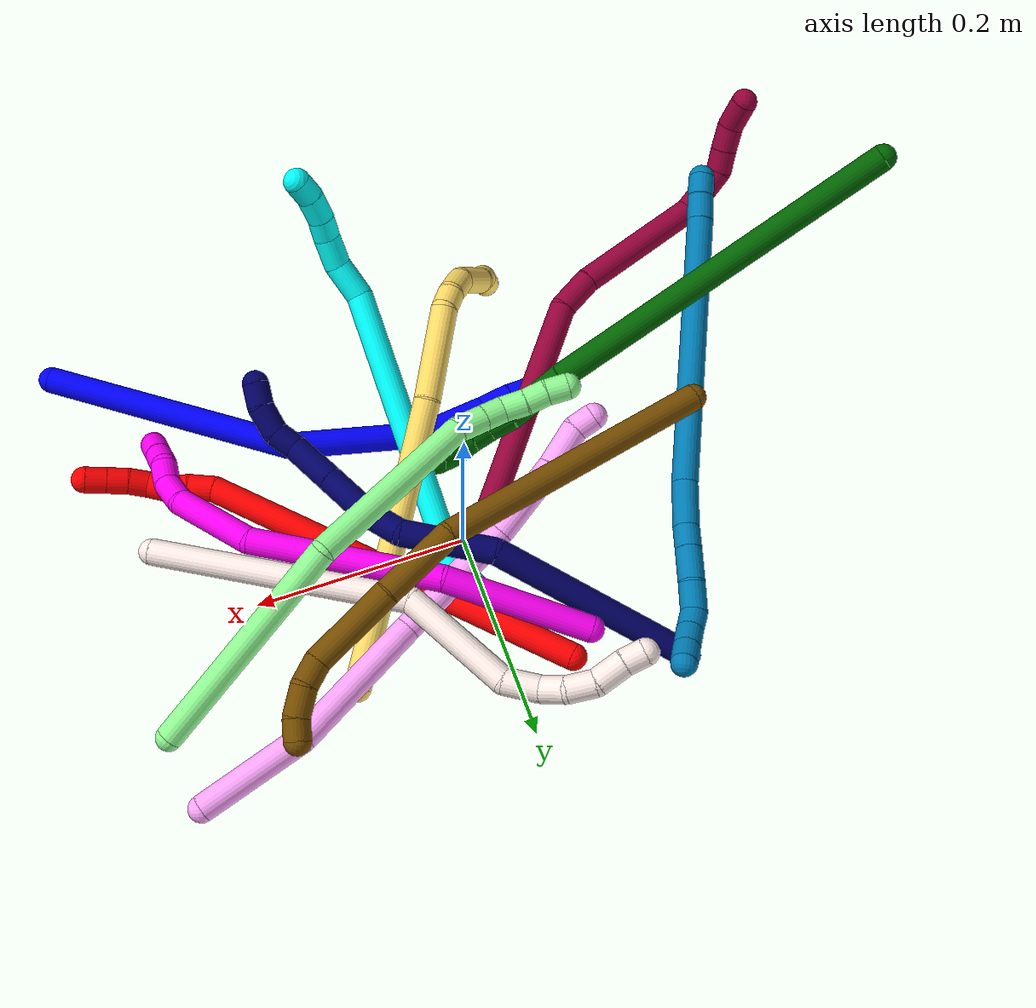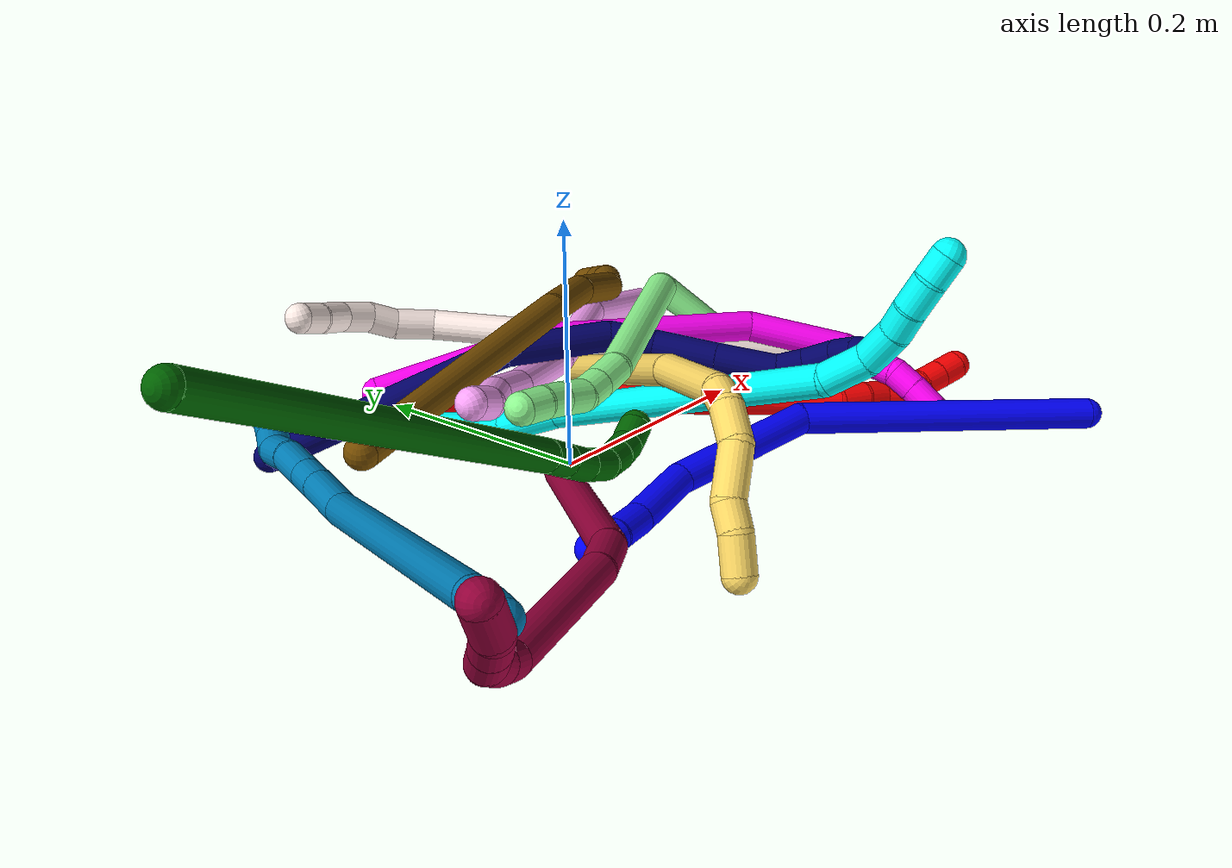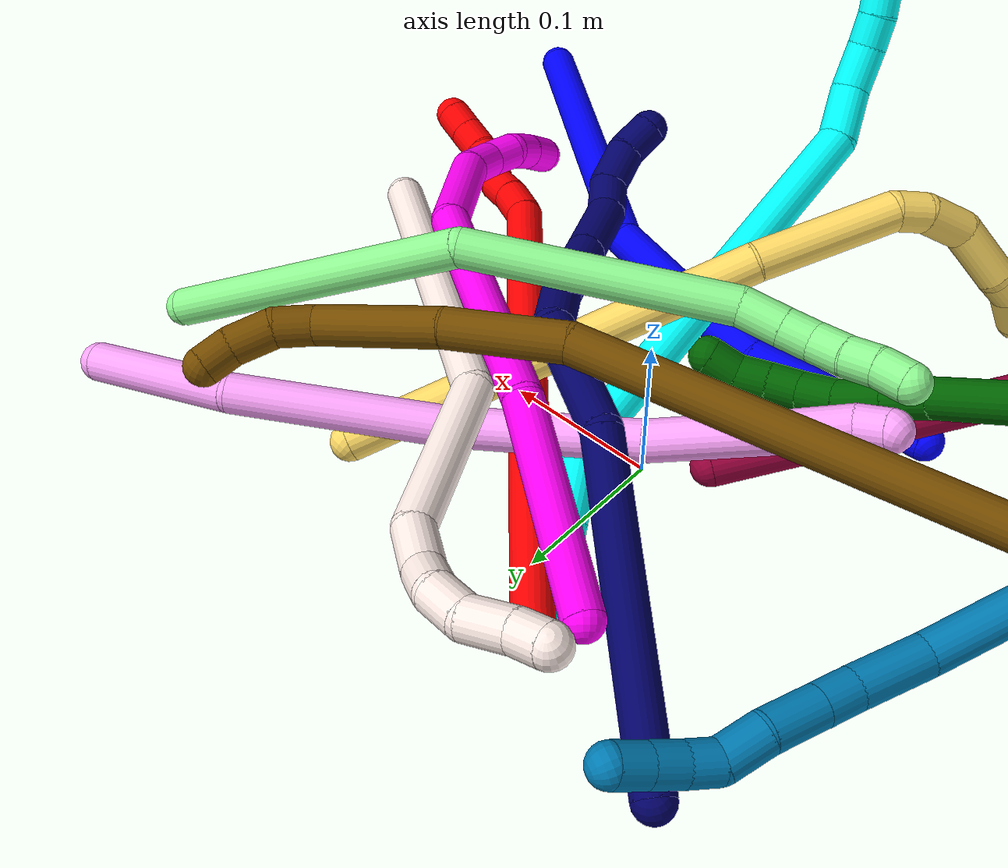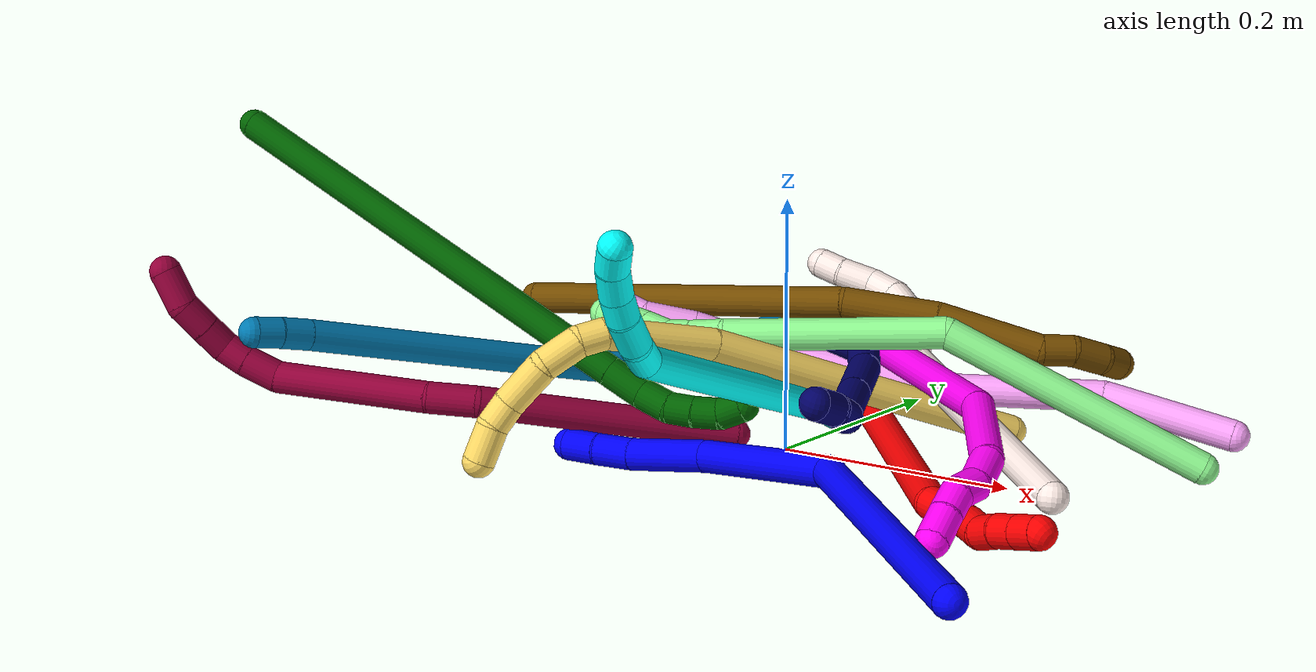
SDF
<sdf version="1.7">
 <world name="default">
  <plugin name="TubeGeneratorPlugin" filename="libtube_generator_plugin.so"/>
  <model name="photoneo_s_sensor">
   <static>1</static>
   <pose>0 0 2 1.57079 1.57079 3.14159</pose>
   <link name="link">
    <inertial><mass>0.1</mass></inertial>
    <sensor name="sensor" type="depth">
     <update_rate>30</update_rate>
     <camera>
      <horizontal_fov>1.22</horizontal_fov>
      <image><width>1920</width><height>1200</height><format>B8G8R8</format></image>
      <clip><near>0.1</near><far>4</far></clip>
      <depth_camera><output>points</output></depth_camera>
     </camera>
     <plugin name="camera_plugin" filename="libgazebo_ros_depth_camera.so">
      <baseline>0.2</baseline>
      <alwaysOn>1</alwaysOn>
      <updateRate>0.0</updateRate>
      <cameraName>camera_ir</cameraName>
      <imageTopicName>/camera/color/image_raw</imageTopicName>
      <cameraInfoTopicName>/camera/color/camera_info</cameraInfoTopicName>
      <depthImageTopicName>/camera/depth/image_raw</depthImageTopicName>
      <depthImageCameraInfoTopicName>/camera/depth/camera_info</depthImageCameraInfoTopicName>
      <pointCloudTopicName>/camera/depth/points</pointCloudTopicName>
      <frameName>fr_optical</frameName>
      <pointCloudCutoff>0.1</pointCloudCutoff>
      <pointCloudCutoffMax>2.0</pointCloudCutoffMax>
      <distortionK1>0</distortionK1>
      <distortionK2>0</distortionK2>
      <distortionK3>0</distortionK3>
      <distortionT1>0</distortionT1>
      <distortionT2>0</distortionT2>
      <CxPrime>0</CxPrime>
      <Cx>0</Cx>
      <Cy>0</Cy>
      <focalLength>0</focalLength>
      <hackBaseline>0</hackBaseline>
     </plugin>
    </sensor>
   </link>
  </model>
  <gravity>0 0 -9.8</gravity>
  <magnetic_field>6e-06 2.3e-05 -4.2e-05</magnetic_field>
  <atmosphere type="adiabatic"/>
  <physics name="default_physics" default="0" type="ode">
   <max_step_size>0.003</max_step_size>
   <real_time_factor>1</real_time_factor>
   <real_time_update_rate>1000</real_time_update_rate>
   <max_contacts>10000</max_contacts>
   <ode>
    <solver>
     <type>quick</type>
     <iters>100</iters>
     <sor>1.3</sor>
     <use_dynamic_moi_rescaling>0</use_dynamic_moi_rescaling>
    </solver>
    <constraints>
     <contact_max_correcting_vel>0</contact_max_correcting_vel>
     <contact_surface_layer>0.001</contact_surface_layer>
     <cfm>0</cfm>
     <erp>0.2</erp>
    </constraints>
   </ode>
  </physics>
  <scene><ambient>0.4 0.4 0.4 1</ambient><background>0.7 0.7 0.7 1</background><shadows>0</shadows></scene>
  <audio><device>default</device></audio>
  <spherical_coordinates>
   <surface_model>EARTH_WGS84</surface_model>
   <latitude_deg>0</latitude_deg>
   <longitude_deg>0</longitude_deg>
   <elevation>0</elevation>
   <heading_deg>0</heading_deg>
  </spherical_coordinates>
  <model name="bin">
   <static>1</static>
   <link name="bottom">
    <collision name="collision-bottom">
     <pose>0 0 -0.01 0 -0 0</pose>
     <geometry><box><size>0.8 0.6 0.02</size></box></geometry>
     <surface>
      <friction><ode><mu>100</mu><mu2>100</mu2></ode></friction>
      <contact><collide_bitmask>65535</collide_bitmask></contact>
     </surface>
    </collision>
   </link>
   <link name="west_wall">
    <collision name="collision-west_wall">
     <pose>-0.41 0 0.1 0 -0 0</pose>
     <geometry><box><size>0.02 0.6 0.2</size></box></geometry>
     <surface>
      <friction><ode><mu>100</mu><mu2>100</mu2></ode></friction>
      <contact><collide_bitmask>65535</collide_bitmask></contact>
     </surface>
    </collision>
   </link>
   <link name="east_wall">
    <collision name="collision-east_wall">
     <pose>0.41 0 0.1 0 -0 0</pose>
     <geometry><box><size>0.02 0.6 0.2</size></box></geometry>
     <surface>
      <friction><ode><mu>100</mu><mu2>100</mu2></ode></friction>
      <contact><collide_bitmask>65535</collide_bitmask></contact>
     </surface>
    </collision>
   </link>
   <link name="south_wall">
    <collision name="collision-south_wall">
     <pose>0 -0.31 0.1 0 -0 0</pose>
     <geometry><box><size>0.8 0.02 0.2</size></box></geometry>
     <surface>
      <friction><ode><mu>100</mu><mu2>100</mu2></ode></friction>
      <contact><collide_bitmask>65535</collide_bitmask></contact>
     </surface>
    </collision>
   </link>
   <link name="north_wall">
    <collision name="collision-north_wall">
     <pose>0 0.31 0.1 0 -0 0</pose>
     <geometry><box><size>0.8 0.02 0.2</size></box></geometry>
     <surface>
      <friction><ode><mu>100</mu><mu2>100</mu2></ode></friction>
      <contact><collide_bitmask>65535</collide_bitmask></contact>
     </surface>
    </collision>
   </link>
  </model>
  <model name="1">
   <static>0</static>
   <link name="1">
    <collision name="collision-cylinder-e_1_1_4">
     <pose>0.025515 0.014249 -0.1216 -3.02494 0.205457 -2.1109</pose>
     <geometry><cylinder><radius>0.0125</radius><length>0.250125</length></cylinder></geometry>
     <surface>
      <friction><ode><mu>1.16</mu><mu2>1.16</mu2><slip1>0</slip1><slip2>0</slip2></ode></friction>
      <contact><ode><kp>1e+06</kp><kd>1</kd><max_vel>0</max_vel><min_depth>0.001</min_depth></ode></contact>
     </surface>
    </collision>
    <visual name="visual-cylinder-e_1_1_4">
     <pose>0.025515 0.014249 -0.1216 -3.02494 0.205457 -2.1109</pose>
     <geometry><cylinder><radius>0.0125</radius><length>0.250125</length></cylinder></geometry>
     <material><ambient>0 0 1 1</ambient></material>
    </visual>
    <collision name="collision-cylinder-e_2_4_5">
     <pose>0.032211 0.027229 -0.304755 3.12096 -0.29664 -3.00372</pose>
     <geometry><cylinder><radius>0.0125</radius><length>0.128759</length></cylinder></geometry>
     <surface>
      <friction><ode><mu>1.16</mu><mu2>1.16</mu2><slip1>0</slip1><slip2>0</slip2></ode></friction>
      <contact><ode><kp>1e+06</kp><kd>1</kd><max_vel>0</max_vel><min_depth>0.001</min_depth></ode></contact>
     </surface>
    </collision>
    <visual name="visual-cylinder-e_2_4_5">
     <pose>0.032211 0.027229 -0.304755 3.12096 -0.29664 -3.00372</pose>
     <geometry><cylinder><radius>0.0125</radius><length>0.128759</length></cylinder></geometry>
     <material><ambient>0 0 1 1</ambient></material>
    </visual>
    <collision name="collision-cylinder-e_3_5_6">
     <pose>-0.005569 0.026463 -0.391741 -3.12174 -0.640577 3.08176</pose>
     <geometry><cylinder><radius>0.0125</radius><length>0.063452</length></cylinder></geometry>
     <surface>
      <friction><ode><mu>1.16</mu><mu2>1.16</mu2><slip1>0</slip1><slip2>0</slip2></ode></friction>
      <contact><ode><kp>1e+06</kp><kd>1</kd><max_vel>0</max_vel><min_depth>0.001</min_depth></ode></contact>
     </surface>
    </collision>
    <visual name="visual-cylinder-e_3_5_6">
     <pose>-0.005569 0.026463 -0.391741 -3.12174 -0.640577 3.08176</pose>
     <geometry><cylinder><radius>0.0125</radius><length>0.063452</length></cylinder></geometry>
     <material><ambient>0 0 1 1</ambient></material>
    </visual>
    <collision name="collision-cylinder-e_4_6_7">
     <pose>-0.033254 0.028847 -0.429158 -2.9861 -0.623425 2.66714</pose>
     <geometry><cylinder><radius>0.0125</radius><length>0.029885</length></cylinder></geometry>
     <surface>
      <friction><ode><mu>1.16</mu><mu2>1.16</mu2><slip1>0</slip1><slip2>0</slip2></ode></friction>
      <contact><ode><kp>1e+06</kp><kd>1</kd><max_vel>0</max_vel><min_depth>0.001</min_depth></ode></contact>
     </surface>
    </collision>
    <visual name="visual-cylinder-e_4_6_7">
     <pose>-0.033254 0.028847 -0.429158 -2.9861 -0.623425 2.66714</pose>
     <geometry><cylinder><radius>0.0125</radius><length>0.029885</length></cylinder></geometry>
     <material><ambient>0 0 1 1</ambient></material>
    </visual>
    <collision name="collision-cylinder-e_5_7_2">
     <pose>-0.048687 0.032087 -0.453228 -3.02945 -0.504123 2.71242</pose>
     <geometry><cylinder><radius>0.0125</radius><length>0.027779</length></cylinder></geometry>
     <surface>
      <friction><ode><mu>1.16</mu><mu2>1.16</mu2><slip1>0</slip1><slip2>0</slip2></ode></friction>
      <contact><ode><kp>1e+06</kp><kd>1</kd><max_vel>0</max_vel><min_depth>0.001</min_depth></ode></contact>
     </surface>
    </collision>
    <visual name="visual-cylinder-e_5_7_2">
     <pose>-0.048687 0.032087 -0.453228 -3.02945 -0.504123 2.71242</pose>
     <geometry><cylinder><radius>0.0125</radius><length>0.027779</length></cylinder></geometry>
     <material><ambient>0 0 1 1</ambient></material>
    </visual>
    <collision name="collision-sphere-2">
     <pose>-0.055396 0.033448 -0.465313 0 -0 0</pose>
     <geometry><sphere><radius>0.0125</radius></sphere></geometry>
     <surface>
      <friction><ode><mu>1.16</mu><mu2>1.16</mu2><slip1>0</slip1><slip2>0</slip2></ode></friction>
      <contact><ode><kp>1e+06</kp><kd>1</kd><max_vel>0</max_vel><min_depth>0.001</min_depth></ode></contact>
     </surface>
    </collision>
    <visual name="visual-sphere-2">
     <pose>-0.055396 0.033448 -0.465313 0 -0 0</pose>
     <geometry><sphere><radius>0.0125</radius></sphere></geometry>
     <material><ambient>0 0 1 1</ambient></material>
    </visual>
    <collision name="collision-sphere-7">
     <pose>-0.041978 0.030726 -0.441143 0 -0 0</pose>
     <geometry><sphere><radius>0.0125</radius></sphere></geometry>
     <surface>
      <friction><ode><mu>1.16</mu><mu2>1.16</mu2><slip1>0</slip1><slip2>0</slip2></ode></friction>
      <contact><ode><kp>1e+06</kp><kd>1</kd><max_vel>0</max_vel><min_depth>0.001</min_depth></ode></contact>
     </surface>
    </collision>
    <visual name="visual-sphere-7">
     <pose>-0.041978 0.030726 -0.441143 0 -0 0</pose>
     <geometry><sphere><radius>0.0125</radius></sphere></geometry>
     <material><ambient>0 0 1 1</ambient></material>
    </visual>
    <collision name="collision-sphere-6">
     <pose>-0.024531 0.026968 -0.417173 0 -0 0</pose>
     <geometry><sphere><radius>0.0125</radius></sphere></geometry>
     <surface>
      <friction><ode><mu>1.16</mu><mu2>1.16</mu2><slip1>0</slip1><slip2>0</slip2></ode></friction>
      <contact><ode><kp>1e+06</kp><kd>1</kd><max_vel>0</max_vel><min_depth>0.001</min_depth></ode></contact>
     </surface>
    </collision>
    <visual name="visual-sphere-6">
     <pose>-0.024531 0.026968 -0.417173 0 -0 0</pose>
     <geometry><sphere><radius>0.0125</radius></sphere></geometry>
     <material><ambient>0 0 1 1</ambient></material>
    </visual>
    <collision name="collision-sphere-5">
     <pose>0.013392 0.025958 -0.36631 0 -0 0</pose>
     <geometry><sphere><radius>0.0125</radius></sphere></geometry>
     <surface>
      <friction><ode><mu>1.16</mu><mu2>1.16</mu2><slip1>0</slip1><slip2>0</slip2></ode></friction>
      <contact><ode><kp>1e+06</kp><kd>1</kd><max_vel>0</max_vel><min_depth>0.001</min_depth></ode></contact>
     </surface>
    </collision>
    <visual name="visual-sphere-5">
     <pose>0.013392 0.025958 -0.36631 0 -0 0</pose>
     <geometry><sphere><radius>0.0125</radius></sphere></geometry>
     <material><ambient>0 0 1 1</ambient></material>
    </visual>
    <collision name="collision-sphere-1">
     <geometry><sphere><radius>0.0125</radius></sphere></geometry>
     <surface>
      <friction><ode><mu>1.16</mu><mu2>1.16</mu2><slip1>0</slip1><slip2>0</slip2></ode></friction>
      <contact><ode><kp>1e+06</kp><kd>1</kd><max_vel>0</max_vel><min_depth>0.001</min_depth></ode></contact>
     </surface>
    </collision>
    <visual name="visual-sphere-1">
     <geometry><sphere><radius>0.0125</radius></sphere></geometry>
     <material><ambient>0 0 1 1</ambient></material>
    </visual>
    <collision name="collision-sphere-4">
     <pose>0.051029 0.028499 -0.243201 0 -0 0</pose>
     <geometry><sphere><radius>0.0125</radius></sphere></geometry>
     <surface>
      <friction><ode><mu>1.16</mu><mu2>1.16</mu2><slip1>0</slip1><slip2>0</slip2></ode></friction>
      <contact><ode><kp>1e+06</kp><kd>1</kd><max_vel>0</max_vel><min_depth>0.001</min_depth></ode></contact>
     </surface>
    </collision>
    <visual name="visual-sphere-4">
     <pose>0.051029 0.028499 -0.243201 0 -0 0</pose>
     <geometry><sphere><radius>0.0125</radius></sphere></geometry>
     <material><ambient>0 0 1 1</ambient></material>
    </visual>
    <inertial>
     <pose>0.015659 0.021005 -0.239855 0 -0 0</pose>
     <mass>0.5</mass>
     <inertia>
      <ixx>-0.001986</ixx>
      <ixy>0</ixy>
      <ixz>0</ixz>
      <iyy>-0.000213</iyy>
      <iyz>0</iyz>
      <izz>-0.000381</izz>
     </inertia>
    </inertial>
   </link>
   <pose>0.32193 -0.287919 0.011499 1.51405 -0.110709 1.09783</pose>
  </model>
  <model name="2">
   <static>0</static>
   <link name="2">
    <collision name="collision-cylinder-e_1_1_4">
     <pose>0.103837 -0.074644 -0.13721 2.64336 0.58669 1.74166</pose>
     <geometry><cylinder><radius>0.0125</radius><length>0.375129</length></cylinder></geometry>
     <surface>
      <friction><ode><mu>1.16</mu><mu2>1.16</mu2><slip1>0</slip1><slip2>0</slip2></ode></friction>
      <contact><ode><kp>1e+06</kp><kd>1</kd><max_vel>0</max_vel><min_depth>0.001</min_depth></ode></contact>
     </surface>
    </collision>
    <visual name="visual-cylinder-e_1_1_4">
     <pose>0.103837 -0.074644 -0.13721 2.64336 0.58669 1.74166</pose>
     <geometry><cylinder><radius>0.0125</radius><length>0.375129</length></cylinder></geometry>
     <material><ambient>1 0 0 1</ambient></material>
    </visual>
    <collision name="collision-cylinder-e_2_4_5">
     <pose>0.213124 -0.150231 -0.285324 3.05542 0.461964 2.77899</pose>
     <geometry><cylinder><radius>0.0125</radius><length>0.024452</length></cylinder></geometry>
     <surface>
      <friction><ode><mu>1.16</mu><mu2>1.16</mu2><slip1>0</slip1><slip2>0</slip2></ode></friction>
      <contact><ode><kp>1e+06</kp><kd>1</kd><max_vel>0</max_vel><min_depth>0.001</min_depth></ode></contact>
     </surface>
    </collision>
    <visual name="visual-cylinder-e_2_4_5">
     <pose>0.213124 -0.150231 -0.285324 3.05542 0.461964 2.77899</pose>
     <geometry><cylinder><radius>0.0125</radius><length>0.024452</length></cylinder></geometry>
     <material><ambient>1 0 0 1</ambient></material>
    </visual>
    <collision name="collision-cylinder-e_3_5_6">
     <pose>0.221786 -0.151277 -0.305787 3.13069 0.324186 3.07493</pose>
     <geometry><cylinder><radius>0.0125</radius><length>0.020171</length></cylinder></geometry>
     <surface>
      <friction><ode><mu>1.16</mu><mu2>1.16</mu2><slip1>0</slip1><slip2>0</slip2></ode></friction>
      <contact><ode><kp>1e+06</kp><kd>1</kd><max_vel>0</max_vel><min_depth>0.001</min_depth></ode></contact>
     </surface>
    </collision>
    <visual name="visual-cylinder-e_3_5_6">
     <pose>0.221786 -0.151277 -0.305787 3.13069 0.324186 3.07493</pose>
     <geometry><cylinder><radius>0.0125</radius><length>0.020171</length></cylinder></geometry>
     <material><ambient>1 0 0 1</ambient></material>
    </visual>
    <collision name="collision-cylinder-e_4_6_7">
     <pose>0.229701 -0.153856 -0.323886 2.85953 0.486568 2.10243</pose>
     <geometry><cylinder><radius>0.0125</radius><length>0.020115</length></cylinder></geometry>
     <surface>
      <friction><ode><mu>1.16</mu><mu2>1.16</mu2><slip1>0</slip1><slip2>0</slip2></ode></friction>
      <contact><ode><kp>1e+06</kp><kd>1</kd><max_vel>0</max_vel><min_depth>0.001</min_depth></ode></contact>
     </surface>
    </collision>
    <visual name="visual-cylinder-e_4_6_7">
     <pose>0.229701 -0.153856 -0.323886 2.85953 0.486568 2.10243</pose>
     <geometry><cylinder><radius>0.0125</radius><length>0.020115</length></cylinder></geometry>
     <material><ambient>1 0 0 1</ambient></material>
    </visual>
    <collision name="collision-cylinder-e_5_7_8">
     <pose>0.241048 -0.154807 -0.339748 -2.93649 0.72633 -2.61266</pose>
     <geometry><cylinder><radius>0.0125</radius><length>0.020009</length></cylinder></geometry>
     <surface>
      <friction><ode><mu>1.16</mu><mu2>1.16</mu2><slip1>0</slip1><slip2>0</slip2></ode></friction>
      <contact><ode><kp>1e+06</kp><kd>1</kd><max_vel>0</max_vel><min_depth>0.001</min_depth></ode></contact>
     </surface>
    </collision>
    <visual name="visual-cylinder-e_5_7_8">
     <pose>0.241048 -0.154807 -0.339748 -2.93649 0.72633 -2.61266</pose>
     <geometry><cylinder><radius>0.0125</radius><length>0.020009</length></cylinder></geometry>
     <material><ambient>1 0 0 1</ambient></material>
    </visual>
    <collision name="collision-cylinder-e_6_8_9">
     <pose>0.253131 -0.151403 -0.355261 -2.9159 0.574396 -2.40885</pose>
     <geometry><cylinder><radius>0.0125</radius><length>0.02002</length></cylinder></geometry>
     <surface>
      <friction><ode><mu>1.16</mu><mu2>1.16</mu2><slip1>0</slip1><slip2>0</slip2></ode></friction>
      <contact><ode><kp>1e+06</kp><kd>1</kd><max_vel>0</max_vel><min_depth>0.001</min_depth></ode></contact>
     </surface>
    </collision>
    <visual name="visual-cylinder-e_6_8_9">
     <pose>0.253131 -0.151403 -0.355261 -2.9159 0.574396 -2.40885</pose>
     <geometry><cylinder><radius>0.0125</radius><length>0.02002</length></cylinder></geometry>
     <material><ambient>1 0 0 1</ambient></material>
    </visual>
    <collision name="collision-cylinder-e_7_9_2">
     <pose>0.264146 -0.147614 -0.371594 -2.91142 0.588039 -2.41222</pose>
     <geometry><cylinder><radius>0.0125</radius><length>0.020103</length></cylinder></geometry>
     <surface>
      <friction><ode><mu>1.16</mu><mu2>1.16</mu2><slip1>0</slip1><slip2>0</slip2></ode></friction>
      <contact><ode><kp>1e+06</kp><kd>1</kd><max_vel>0</max_vel><min_depth>0.001</min_depth></ode></contact>
     </surface>
    </collision>
    <visual name="visual-cylinder-e_7_9_2">
     <pose>0.264146 -0.147614 -0.371594 -2.91142 0.588039 -2.41222</pose>
     <geometry><cylinder><radius>0.0125</radius><length>0.020103</length></cylinder></geometry>
     <material><ambient>1 0 0 1</ambient></material>
    </visual>
    <collision name="collision-sphere-2">
     <pose>0.269722 -0.145706 -0.379737 0 -0 0</pose>
     <geometry><sphere><radius>0.0125</radius></sphere></geometry>
     <surface>
      <friction><ode><mu>1.16</mu><mu2>1.16</mu2><slip1>0</slip1><slip2>0</slip2></ode></friction>
      <contact><ode><kp>1e+06</kp><kd>1</kd><max_vel>0</max_vel><min_depth>0.001</min_depth></ode></contact>
     </surface>
    </collision>
    <visual name="visual-sphere-2">
     <pose>0.269722 -0.145706 -0.379737 0 -0 0</pose>
     <geometry><sphere><radius>0.0125</radius></sphere></geometry>
     <material><ambient>1 0 0 1</ambient></material>
    </visual>
    <collision name="collision-sphere-9">
     <pose>0.25857 -0.149522 -0.363451 0 -0 0</pose>
     <geometry><sphere><radius>0.0125</radius></sphere></geometry>
     <surface>
      <friction><ode><mu>1.16</mu><mu2>1.16</mu2><slip1>0</slip1><slip2>0</slip2></ode></friction>
      <contact><ode><kp>1e+06</kp><kd>1</kd><max_vel>0</max_vel><min_depth>0.001</min_depth></ode></contact>
     </surface>
    </collision>
    <visual name="visual-sphere-9">
     <pose>0.25857 -0.149522 -0.363451 0 -0 0</pose>
     <geometry><sphere><radius>0.0125</radius></sphere></geometry>
     <material><ambient>1 0 0 1</ambient></material>
    </visual>
    <collision name="collision-sphere-4">
     <pose>0.207674 -0.149289 -0.27442 0 -0 0</pose>
     <geometry><sphere><radius>0.0125</radius></sphere></geometry>
     <surface>
      <friction><ode><mu>1.16</mu><mu2>1.16</mu2><slip1>0</slip1><slip2>0</slip2></ode></friction>
      <contact><ode><kp>1e+06</kp><kd>1</kd><max_vel>0</max_vel><min_depth>0.001</min_depth></ode></contact>
     </surface>
    </collision>
    <visual name="visual-sphere-4">
     <pose>0.207674 -0.149289 -0.27442 0 -0 0</pose>
     <geometry><sphere><radius>0.0125</radius></sphere></geometry>
     <material><ambient>1 0 0 1</ambient></material>
    </visual>
    <collision name="collision-sphere-1">
     <geometry><sphere><radius>0.0125</radius></sphere></geometry>
     <surface>
      <friction><ode><mu>1.16</mu><mu2>1.16</mu2><slip1>0</slip1><slip2>0</slip2></ode></friction>
      <contact><ode><kp>1e+06</kp><kd>1</kd><max_vel>0</max_vel><min_depth>0.001</min_depth></ode></contact>
     </surface>
    </collision>
    <visual name="visual-sphere-1">
     <geometry><sphere><radius>0.0125</radius></sphere></geometry>
     <material><ambient>1 0 0 1</ambient></material>
    </visual>
    <collision name="collision-sphere-8">
     <pose>0.247693 -0.153283 -0.34707 0 -0 0</pose>
     <geometry><sphere><radius>0.0125</radius></sphere></geometry>
     <surface>
      <friction><ode><mu>1.16</mu><mu2>1.16</mu2><slip1>0</slip1><slip2>0</slip2></ode></friction>
      <contact><ode><kp>1e+06</kp><kd>1</kd><max_vel>0</max_vel><min_depth>0.001</min_depth></ode></contact>
     </surface>
    </collision>
    <visual name="visual-sphere-8">
     <pose>0.247693 -0.153283 -0.34707 0 -0 0</pose>
     <geometry><sphere><radius>0.0125</radius></sphere></geometry>
     <material><ambient>1 0 0 1</ambient></material>
    </visual>
    <collision name="collision-sphere-5">
     <pose>0.218573 -0.151173 -0.296228 0 -0 0</pose>
     <geometry><sphere><radius>0.0125</radius></sphere></geometry>
     <surface>
      <friction><ode><mu>1.16</mu><mu2>1.16</mu2><slip1>0</slip1><slip2>0</slip2></ode></friction>
      <contact><ode><kp>1e+06</kp><kd>1</kd><max_vel>0</max_vel><min_depth>0.001</min_depth></ode></contact>
     </surface>
    </collision>
    <visual name="visual-sphere-5">
     <pose>0.218573 -0.151173 -0.296228 0 -0 0</pose>
     <geometry><sphere><radius>0.0125</radius></sphere></geometry>
     <material><ambient>1 0 0 1</ambient></material>
    </visual>
    <collision name="collision-sphere-6">
     <pose>0.224998 -0.151381 -0.315347 0 -0 0</pose>
     <geometry><sphere><radius>0.0125</radius></sphere></geometry>
     <surface>
      <friction><ode><mu>1.16</mu><mu2>1.16</mu2><slip1>0</slip1><slip2>0</slip2></ode></friction>
      <contact><ode><kp>1e+06</kp><kd>1</kd><max_vel>0</max_vel><min_depth>0.001</min_depth></ode></contact>
     </surface>
    </collision>
    <visual name="visual-sphere-6">
     <pose>0.224998 -0.151381 -0.315347 0 -0 0</pose>
     <geometry><sphere><radius>0.0125</radius></sphere></geometry>
     <material><ambient>1 0 0 1</ambient></material>
    </visual>
    <collision name="collision-sphere-7">
     <pose>0.234404 -0.15633 -0.332425 0 -0 0</pose>
     <geometry><sphere><radius>0.0125</radius></sphere></geometry>
     <surface>
      <friction><ode><mu>1.16</mu><mu2>1.16</mu2><slip1>0</slip1><slip2>0</slip2></ode></friction>
      <contact><ode><kp>1e+06</kp><kd>1</kd><max_vel>0</max_vel><min_depth>0.001</min_depth></ode></contact>
     </surface>
    </collision>
    <visual name="visual-sphere-7">
     <pose>0.234404 -0.15633 -0.332425 0 -0 0</pose>
     <geometry><sphere><radius>0.0125</radius></sphere></geometry>
     <material><ambient>1 0 0 1</ambient></material>
    </visual>
    <inertial>
     <pose>0.136918 -0.093834 -0.185024 0 -0 0</pose>
     <mass>0.5</mass>
     <inertia>
      <ixx>0.003011</ixx>
      <ixy>0</ixy>
      <ixz>0</ixz>
      <iyy>0.005428</iyy>
      <iyz>0</iyz>
      <izz>-0.000722</izz>
     </inertia>
    </inertial>
   </link>
   <pose>-0.050139 0.155041 0.035823 0.878008 -0.899943 -1.13442</pose>
  </model>
  <model name="3">
   <static>0</static>
   <link name="3">
    <collision name="collision-cylinder-e_1_1_4">
     <pose>0.022848 -0.009292 0.010523 0.723326 1.01983 0.416982</pose>
     <geometry><cylinder><radius>0.0125</radius><length>0.053631</length></cylinder></geometry>
     <surface>
      <friction><ode><mu>1.16</mu><mu2>1.16</mu2><slip1>0</slip1><slip2>0</slip2></ode></friction>
      <contact><ode><kp>1e+06</kp><kd>1</kd><max_vel>0</max_vel><min_depth>0.001</min_depth></ode></contact>
     </surface>
    </collision>
    <visual name="visual-cylinder-e_1_1_4">
     <pose>0.022848 -0.009292 0.010523 0.723326 1.01983 0.416982</pose>
     <geometry><cylinder><radius>0.0125</radius><length>0.053631</length></cylinder></geometry>
     <material><ambient>0.003922 1 0.996078 1</ambient></material>
    </visual>
    <collision name="collision-cylinder-e_2_4_5">
     <pose>0.062812 -0.03068 0.035304 0.70361 0.741285 0.283381</pose>
     <geometry><cylinder><radius>0.0125</radius><length>0.050699</length></cylinder></geometry>
     <surface>
      <friction><ode><mu>1.16</mu><mu2>1.16</mu2><slip1>0</slip1><slip2>0</slip2></ode></friction>
      <contact><ode><kp>1e+06</kp><kd>1</kd><max_vel>0</max_vel><min_depth>0.001</min_depth></ode></contact>
     </surface>
    </collision>
    <visual name="visual-cylinder-e_2_4_5">
     <pose>0.062812 -0.03068 0.035304 0.70361 0.741285 0.283381</pose>
     <geometry><cylinder><radius>0.0125</radius><length>0.050699</length></cylinder></geometry>
     <material><ambient>0.003922 1 0.996078 1</ambient></material>
    </visual>
    <collision name="collision-cylinder-e_3_5_6">
     <pose>0.146593 -0.151249 0.086439 1.24308 0.526984 0.381726</pose>
     <geometry><cylinder><radius>0.0125</radius><length>0.265106</length></cylinder></geometry>
     <surface>
      <friction><ode><mu>1.16</mu><mu2>1.16</mu2><slip1>0</slip1><slip2>0</slip2></ode></friction>
      <contact><ode><kp>1e+06</kp><kd>1</kd><max_vel>0</max_vel><min_depth>0.001</min_depth></ode></contact>
     </surface>
    </collision>
    <visual name="visual-cylinder-e_3_5_6">
     <pose>0.146593 -0.151249 0.086439 1.24308 0.526984 0.381726</pose>
     <geometry><cylinder><radius>0.0125</radius><length>0.265106</length></cylinder></geometry>
     <material><ambient>0.003922 1 0.996078 1</ambient></material>
    </visual>
    <collision name="collision-cylinder-e_4_6_7">
     <pose>0.221561 -0.270539 0.13448 0.769698 0.490553 0.202089</pose>
     <geometry><cylinder><radius>0.0125</radius><length>0.035248</length></cylinder></geometry>
     <surface>
      <friction><ode><mu>1.16</mu><mu2>1.16</mu2><slip1>0</slip1><slip2>0</slip2></ode></friction>
      <contact><ode><kp>1e+06</kp><kd>1</kd><max_vel>0</max_vel><min_depth>0.001</min_depth></ode></contact>
     </surface>
    </collision>
    <visual name="visual-cylinder-e_4_6_7">
     <pose>0.221561 -0.270539 0.13448 0.769698 0.490553 0.202089</pose>
     <geometry><cylinder><radius>0.0125</radius><length>0.035248</length></cylinder></geometry>
     <material><ambient>0.003922 1 0.996078 1</ambient></material>
    </visual>
    <collision name="collision-cylinder-e_5_7_8">
     <pose>0.231677 -0.292075 0.15563 0.820693 0.123168 0.053638</pose>
     <geometry><cylinder><radius>0.0125</radius><length>0.029522</length></cylinder></geometry>
     <surface>
      <friction><ode><mu>1.16</mu><mu2>1.16</mu2><slip1>0</slip1><slip2>0</slip2></ode></friction>
      <contact><ode><kp>1e+06</kp><kd>1</kd><max_vel>0</max_vel><min_depth>0.001</min_depth></ode></contact>
     </surface>
    </collision>
    <visual name="visual-cylinder-e_5_7_8">
     <pose>0.231677 -0.292075 0.15563 0.820693 0.123168 0.053638</pose>
     <geometry><cylinder><radius>0.0125</radius><length>0.029522</length></cylinder></geometry>
     <material><ambient>0.003922 1 0.996078 1</ambient></material>
    </visual>
    <collision name="collision-cylinder-e_6_8_9">
     <pose>0.232893 -0.309692 0.173043 0.748618 -0.058849 -0.023123</pose>
     <geometry><cylinder><radius>0.0125</radius><length>0.020309</length></cylinder></geometry>
     <surface>
      <friction><ode><mu>1.16</mu><mu2>1.16</mu2><slip1>0</slip1><slip2>0</slip2></ode></friction>
      <contact><ode><kp>1e+06</kp><kd>1</kd><max_vel>0</max_vel><min_depth>0.001</min_depth></ode></contact>
     </surface>
    </collision>
    <visual name="visual-cylinder-e_6_8_9">
     <pose>0.232893 -0.309692 0.173043 0.748618 -0.058849 -0.023123</pose>
     <geometry><cylinder><radius>0.0125</radius><length>0.020309</length></cylinder></geometry>
     <material><ambient>0.003922 1 0.996078 1</ambient></material>
    </visual>
    <collision name="collision-cylinder-e_7_9_10">
     <pose>0.232578 -0.323891 0.190442 0.631836 0.022778 0.007446</pose>
     <geometry><cylinder><radius>0.0125</radius><length>0.024724</length></cylinder></geometry>
     <surface>
      <friction><ode><mu>1.16</mu><mu2>1.16</mu2><slip1>0</slip1><slip2>0</slip2></ode></friction>
      <contact><ode><kp>1e+06</kp><kd>1</kd><max_vel>0</max_vel><min_depth>0.001</min_depth></ode></contact>
     </surface>
    </collision>
    <visual name="visual-cylinder-e_7_9_10">
     <pose>0.232578 -0.323891 0.190442 0.631836 0.022778 0.007446</pose>
     <geometry><cylinder><radius>0.0125</radius><length>0.024724</length></cylinder></geometry>
     <material><ambient>0.003922 1 0.996078 1</ambient></material>
    </visual>
    <collision name="collision-cylinder-e_8_10_2">
     <pose>0.23385 -0.335488 0.209813 0.428909 0.095552 0.020827</pose>
     <geometry><cylinder><radius>0.0125</radius><length>0.020762</length></cylinder></geometry>
     <surface>
      <friction><ode><mu>1.16</mu><mu2>1.16</mu2><slip1>0</slip1><slip2>0</slip2></ode></friction>
      <contact><ode><kp>1e+06</kp><kd>1</kd><max_vel>0</max_vel><min_depth>0.001</min_depth></ode></contact>
     </surface>
    </collision>
    <visual name="visual-cylinder-e_8_10_2">
     <pose>0.23385 -0.335488 0.209813 0.428909 0.095552 0.020827</pose>
     <geometry><cylinder><radius>0.0125</radius><length>0.020762</length></cylinder></geometry>
     <material><ambient>0.003922 1 0.996078 1</ambient></material>
    </visual>
    <collision name="collision-sphere-2">
     <pose>0.23484 -0.339785 0.21921 0 -0 0</pose>
     <geometry><sphere><radius>0.0125</radius></sphere></geometry>
     <surface>
      <friction><ode><mu>1.16</mu><mu2>1.16</mu2><slip1>0</slip1><slip2>0</slip2></ode></friction>
      <contact><ode><kp>1e+06</kp><kd>1</kd><max_vel>0</max_vel><min_depth>0.001</min_depth></ode></contact>
     </surface>
    </collision>
    <visual name="visual-sphere-2">
     <pose>0.23484 -0.339785 0.21921 0 -0 0</pose>
     <geometry><sphere><radius>0.0125</radius></sphere></geometry>
     <material><ambient>0.003922 1 0.996078 1</ambient></material>
    </visual>
    <collision name="collision-sphere-10">
     <pose>0.232859 -0.33119 0.200415 0 -0 0</pose>
     <geometry><sphere><radius>0.0125</radius></sphere></geometry>
     <surface>
      <friction><ode><mu>1.16</mu><mu2>1.16</mu2><slip1>0</slip1><slip2>0</slip2></ode></friction>
      <contact><ode><kp>1e+06</kp><kd>1</kd><max_vel>0</max_vel><min_depth>0.001</min_depth></ode></contact>
     </surface>
    </collision>
    <visual name="visual-sphere-10">
     <pose>0.232859 -0.33119 0.200415 0 -0 0</pose>
     <geometry><sphere><radius>0.0125</radius></sphere></geometry>
     <material><ambient>0.003922 1 0.996078 1</ambient></material>
    </visual>
    <collision name="collision-sphere-9">
     <pose>0.232296 -0.316591 0.18047 0 -0 0</pose>
     <geometry><sphere><radius>0.0125</radius></sphere></geometry>
     <surface>
      <friction><ode><mu>1.16</mu><mu2>1.16</mu2><slip1>0</slip1><slip2>0</slip2></ode></friction>
      <contact><ode><kp>1e+06</kp><kd>1</kd><max_vel>0</max_vel><min_depth>0.001</min_depth></ode></contact>
     </surface>
    </collision>
    <visual name="visual-sphere-9">
     <pose>0.232296 -0.316591 0.18047 0 -0 0</pose>
     <geometry><sphere><radius>0.0125</radius></sphere></geometry>
     <material><ambient>0.003922 1 0.996078 1</ambient></material>
    </visual>
    <collision name="collision-sphere-4">
     <pose>0.045695 -0.018583 0.021046 0 -0 0</pose>
     <geometry><sphere><radius>0.0125</radius></sphere></geometry>
     <surface>
      <friction><ode><mu>1.16</mu><mu2>1.16</mu2><slip1>0</slip1><slip2>0</slip2></ode></friction>
      <contact><ode><kp>1e+06</kp><kd>1</kd><max_vel>0</max_vel><min_depth>0.001</min_depth></ode></contact>
     </surface>
    </collision>
    <visual name="visual-sphere-4">
     <pose>0.045695 -0.018583 0.021046 0 -0 0</pose>
     <geometry><sphere><radius>0.0125</radius></sphere></geometry>
     <material><ambient>0.003922 1 0.996078 1</ambient></material>
    </visual>
    <collision name="collision-sphere-1">
     <geometry><sphere><radius>0.0125</radius></sphere></geometry>
     <surface>
      <friction><ode><mu>1.16</mu><mu2>1.16</mu2><slip1>0</slip1><slip2>0</slip2></ode></friction>
      <contact><ode><kp>1e+06</kp><kd>1</kd><max_vel>0</max_vel><min_depth>0.001</min_depth></ode></contact>
     </surface>
    </collision>
    <visual name="visual-sphere-1">
     <geometry><sphere><radius>0.0125</radius></sphere></geometry>
     <material><ambient>0.003922 1 0.996078 1</ambient></material>
    </visual>
    <collision name="collision-sphere-8">
     <pose>0.233491 -0.302792 0.165616 0 -0 0</pose>
     <geometry><sphere><radius>0.0125</radius></sphere></geometry>
     <surface>
      <friction><ode><mu>1.16</mu><mu2>1.16</mu2><slip1>0</slip1><slip2>0</slip2></ode></friction>
      <contact><ode><kp>1e+06</kp><kd>1</kd><max_vel>0</max_vel><min_depth>0.001</min_depth></ode></contact>
     </surface>
    </collision>
    <visual name="visual-sphere-8">
     <pose>0.233491 -0.302792 0.165616 0 -0 0</pose>
     <geometry><sphere><radius>0.0125</radius></sphere></geometry>
     <material><ambient>0.003922 1 0.996078 1</ambient></material>
    </visual>
    <collision name="collision-sphere-5">
     <pose>0.079929 -0.042777 0.049561 0 -0 0</pose>
     <geometry><sphere><radius>0.0125</radius></sphere></geometry>
     <surface>
      <friction><ode><mu>1.16</mu><mu2>1.16</mu2><slip1>0</slip1><slip2>0</slip2></ode></friction>
      <contact><ode><kp>1e+06</kp><kd>1</kd><max_vel>0</max_vel><min_depth>0.001</min_depth></ode></contact>
     </surface>
    </collision>
    <visual name="visual-sphere-5">
     <pose>0.079929 -0.042777 0.049561 0 -0 0</pose>
     <geometry><sphere><radius>0.0125</radius></sphere></geometry>
     <material><ambient>0.003922 1 0.996078 1</ambient></material>
    </visual>
    <collision name="collision-sphere-6">
     <pose>0.213258 -0.259721 0.123316 0 -0 0</pose>
     <geometry><sphere><radius>0.0125</radius></sphere></geometry>
     <surface>
      <friction><ode><mu>1.16</mu><mu2>1.16</mu2><slip1>0</slip1><slip2>0</slip2></ode></friction>
      <contact><ode><kp>1e+06</kp><kd>1</kd><max_vel>0</max_vel><min_depth>0.001</min_depth></ode></contact>
     </surface>
    </collision>
    <visual name="visual-sphere-6">
     <pose>0.213258 -0.259721 0.123316 0 -0 0</pose>
     <geometry><sphere><radius>0.0125</radius></sphere></geometry>
     <material><ambient>0.003922 1 0.996078 1</ambient></material>
    </visual>
    <collision name="collision-sphere-7">
     <pose>0.229864 -0.281357 0.145644 0 -0 0</pose>
     <geometry><sphere><radius>0.0125</radius></sphere></geometry>
     <surface>
      <friction><ode><mu>1.16</mu><mu2>1.16</mu2><slip1>0</slip1><slip2>0</slip2></ode></friction>
      <contact><ode><kp>1e+06</kp><kd>1</kd><max_vel>0</max_vel><min_depth>0.001</min_depth></ode></contact>
     </surface>
    </collision>
    <visual name="visual-sphere-7">
     <pose>0.229864 -0.281357 0.145644 0 -0 0</pose>
     <geometry><sphere><radius>0.0125</radius></sphere></geometry>
     <material><ambient>0.003922 1 0.996078 1</ambient></material>
    </visual>
    <inertial>
     <pose>0.146514 -0.163144 0.094366 0 -0 0</pose>
     <mass>0.5</mass>
     <inertia>
      <ixx>0.001811</ixx>
      <ixy>0</ixy>
      <ixz>0</ixz>
      <iyy>0.001263</iyy>
      <iyz>0</iyz>
      <izz>0.000506</izz>
     </inertia>
    </inertial>
   </link>
   <pose>-0.030844 0.118839 0.011269 -0.517674 0.499494 -0.90212</pose>
  </model>
  <model name="4">
   <static>0</static>
   <link name="4">
    <collision name="collision-cylinder-e_1_1_4">
     <pose>-0.018813 -0.005576 -0.049477 3.02937 -0.361262 -2.54482</pose>
     <geometry><cylinder><radius>0.0125</radius><length>0.106451</length></cylinder></geometry>
     <surface>
      <friction><ode><mu>1.16</mu><mu2>1.16</mu2><slip1>0</slip1><slip2>0</slip2></ode></friction>
      <contact><ode><kp>1e+06</kp><kd>1</kd><max_vel>0</max_vel><min_depth>0.001</min_depth></ode></contact>
     </surface>
    </collision>
    <visual name="visual-cylinder-e_1_1_4">
     <pose>-0.018813 -0.005576 -0.049477 3.02937 -0.361262 -2.54482</pose>
     <geometry><cylinder><radius>0.0125</radius><length>0.106451</length></cylinder></geometry>
     <material><ambient>1 0.65098 0.996078 1</ambient></material>
    </visual>
    <collision name="collision-cylinder-e_2_4_5">
     <pose>-0.062071 -0.039736 -0.155614 2.67436 -0.367675 -1.32657</pose>
     <geometry><cylinder><radius>0.0125</radius><length>0.136016</length></cylinder></geometry>
     <surface>
      <friction><ode><mu>1.16</mu><mu2>1.16</mu2><slip1>0</slip1><slip2>0</slip2></ode></friction>
      <contact><ode><kp>1e+06</kp><kd>1</kd><max_vel>0</max_vel><min_depth>0.001</min_depth></ode></contact>
     </surface>
    </collision>
    <visual name="visual-cylinder-e_2_4_5">
     <pose>-0.062071 -0.039736 -0.155614 2.67436 -0.367675 -1.32657</pose>
     <geometry><cylinder><radius>0.0125</radius><length>0.136016</length></cylinder></geometry>
     <material><ambient>1 0.65098 0.996078 1</ambient></material>
    </visual>
    <collision name="collision-cylinder-e_3_5_6">
     <pose>-0.114018 -0.084919 -0.263114 2.82601 -0.474976 -1.97856</pose>
     <geometry><cylinder><radius>0.0125</radius><length>0.120274</length></cylinder></geometry>
     <surface>
      <friction><ode><mu>1.16</mu><mu2>1.16</mu2><slip1>0</slip1><slip2>0</slip2></ode></friction>
      <contact><ode><kp>1e+06</kp><kd>1</kd><max_vel>0</max_vel><min_depth>0.001</min_depth></ode></contact>
     </surface>
    </collision>
    <visual name="visual-cylinder-e_3_5_6">
     <pose>-0.114018 -0.084919 -0.263114 2.82601 -0.474976 -1.97856</pose>
     <geometry><cylinder><radius>0.0125</radius><length>0.120274</length></cylinder></geometry>
     <material><ambient>1 0.65098 0.996078 1</ambient></material>
    </visual>
    <collision name="collision-cylinder-e_4_6_7">
     <pose>-0.16318 -0.110986 -0.343532 2.83181 -0.609004 -2.21937</pose>
     <geometry><cylinder><radius>0.0125</radius><length>0.07573</length></cylinder></geometry>
     <surface>
      <friction><ode><mu>1.16</mu><mu2>1.16</mu2><slip1>0</slip1><slip2>0</slip2></ode></friction>
      <contact><ode><kp>1e+06</kp><kd>1</kd><max_vel>0</max_vel><min_depth>0.001</min_depth></ode></contact>
     </surface>
    </collision>
    <visual name="visual-cylinder-e_4_6_7">
     <pose>-0.16318 -0.110986 -0.343532 2.83181 -0.609004 -2.21937</pose>
     <geometry><cylinder><radius>0.0125</radius><length>0.07573</length></cylinder></geometry>
     <material><ambient>1 0.65098 0.996078 1</ambient></material>
    </visual>
    <collision name="collision-cylinder-e_5_7_8">
     <pose>-0.196515 -0.128441 -0.387974 2.64843 -0.605258 -1.78459</pose>
     <geometry><cylinder><radius>0.0125</radius><length>0.041035</length></cylinder></geometry>
     <surface>
      <friction><ode><mu>1.16</mu><mu2>1.16</mu2><slip1>0</slip1><slip2>0</slip2></ode></friction>
      <contact><ode><kp>1e+06</kp><kd>1</kd><max_vel>0</max_vel><min_depth>0.001</min_depth></ode></contact>
     </surface>
    </collision>
    <visual name="visual-cylinder-e_5_7_8">
     <pose>-0.196515 -0.128441 -0.387974 2.64843 -0.605258 -1.78459</pose>
     <geometry><cylinder><radius>0.0125</radius><length>0.041035</length></cylinder></geometry>
     <material><ambient>1 0.65098 0.996078 1</ambient></material>
    </visual>
    <collision name="collision-cylinder-e_6_8_2">
     <pose>-0.212403 -0.13627 -0.412175 -3.12454 -0.423852 3.06237</pose>
     <geometry><cylinder><radius>0.0125</radius><length>0.020493</length></cylinder></geometry>
     <surface>
      <friction><ode><mu>1.16</mu><mu2>1.16</mu2><slip1>0</slip1><slip2>0</slip2></ode></friction>
      <contact><ode><kp>1e+06</kp><kd>1</kd><max_vel>0</max_vel><min_depth>0.001</min_depth></ode></contact>
     </surface>
    </collision>
    <visual name="visual-cylinder-e_6_8_2">
     <pose>-0.212403 -0.13627 -0.412175 -3.12454 -0.423852 3.06237</pose>
     <geometry><cylinder><radius>0.0125</radius><length>0.020493</length></cylinder></geometry>
     <material><ambient>1 0.65098 0.996078 1</ambient></material>
    </visual>
    <collision name="collision-sphere-2">
     <pose>-0.216617 -0.136111 -0.421513 0 -0 0</pose>
     <geometry><sphere><radius>0.0125</radius></sphere></geometry>
     <surface>
      <friction><ode><mu>1.16</mu><mu2>1.16</mu2><slip1>0</slip1><slip2>0</slip2></ode></friction>
      <contact><ode><kp>1e+06</kp><kd>1</kd><max_vel>0</max_vel><min_depth>0.001</min_depth></ode></contact>
     </surface>
    </collision>
    <visual name="visual-sphere-2">
     <pose>-0.216617 -0.136111 -0.421513 0 -0 0</pose>
     <geometry><sphere><radius>0.0125</radius></sphere></geometry>
     <material><ambient>1 0.65098 0.996078 1</ambient></material>
    </visual>
    <collision name="collision-sphere-4">
     <pose>-0.037626 -0.011151 -0.098953 0 -0 0</pose>
     <geometry><sphere><radius>0.0125</radius></sphere></geometry>
     <surface>
      <friction><ode><mu>1.16</mu><mu2>1.16</mu2><slip1>0</slip1><slip2>0</slip2></ode></friction>
      <contact><ode><kp>1e+06</kp><kd>1</kd><max_vel>0</max_vel><min_depth>0.001</min_depth></ode></contact>
     </surface>
    </collision>
    <visual name="visual-sphere-4">
     <pose>-0.037626 -0.011151 -0.098953 0 -0 0</pose>
     <geometry><sphere><radius>0.0125</radius></sphere></geometry>
     <material><ambient>1 0.65098 0.996078 1</ambient></material>
    </visual>
    <collision name="collision-sphere-1">
     <geometry><sphere><radius>0.0125</radius></sphere></geometry>
     <surface>
      <friction><ode><mu>1.16</mu><mu2>1.16</mu2><slip1>0</slip1><slip2>0</slip2></ode></friction>
      <contact><ode><kp>1e+06</kp><kd>1</kd><max_vel>0</max_vel><min_depth>0.001</min_depth></ode></contact>
     </surface>
    </collision>
    <visual name="visual-sphere-1">
     <geometry><sphere><radius>0.0125</radius></sphere></geometry>
     <material><ambient>1 0.65098 0.996078 1</ambient></material>
    </visual>
    <collision name="collision-sphere-8">
     <pose>-0.208189 -0.136429 -0.402836 0 -0 0</pose>
     <geometry><sphere><radius>0.0125</radius></sphere></geometry>
     <surface>
      <friction><ode><mu>1.16</mu><mu2>1.16</mu2><slip1>0</slip1><slip2>0</slip2></ode></friction>
      <contact><ode><kp>1e+06</kp><kd>1</kd><max_vel>0</max_vel><min_depth>0.001</min_depth></ode></contact>
     </surface>
    </collision>
    <visual name="visual-sphere-8">
     <pose>-0.208189 -0.136429 -0.402836 0 -0 0</pose>
     <geometry><sphere><radius>0.0125</radius></sphere></geometry>
     <material><ambient>1 0.65098 0.996078 1</ambient></material>
    </visual>
    <collision name="collision-sphere-5">
     <pose>-0.086516 -0.068321 -0.212275 0 -0 0</pose>
     <geometry><sphere><radius>0.0125</radius></sphere></geometry>
     <surface>
      <friction><ode><mu>1.16</mu><mu2>1.16</mu2><slip1>0</slip1><slip2>0</slip2></ode></friction>
      <contact><ode><kp>1e+06</kp><kd>1</kd><max_vel>0</max_vel><min_depth>0.001</min_depth></ode></contact>
     </surface>
    </collision>
    <visual name="visual-sphere-5">
     <pose>-0.086516 -0.068321 -0.212275 0 -0 0</pose>
     <geometry><sphere><radius>0.0125</radius></sphere></geometry>
     <material><ambient>1 0.65098 0.996078 1</ambient></material>
    </visual>
    <collision name="collision-sphere-6">
     <pose>-0.14152 -0.101518 -0.313953 0 -0 0</pose>
     <geometry><sphere><radius>0.0125</radius></sphere></geometry>
     <surface>
      <friction><ode><mu>1.16</mu><mu2>1.16</mu2><slip1>0</slip1><slip2>0</slip2></ode></friction>
      <contact><ode><kp>1e+06</kp><kd>1</kd><max_vel>0</max_vel><min_depth>0.001</min_depth></ode></contact>
     </surface>
    </collision>
    <visual name="visual-sphere-6">
     <pose>-0.14152 -0.101518 -0.313953 0 -0 0</pose>
     <geometry><sphere><radius>0.0125</radius></sphere></geometry>
     <material><ambient>1 0.65098 0.996078 1</ambient></material>
    </visual>
    <collision name="collision-sphere-7">
     <pose>-0.184841 -0.120454 -0.373112 0 -0 0</pose>
     <geometry><sphere><radius>0.0125</radius></sphere></geometry>
     <surface>
      <friction><ode><mu>1.16</mu><mu2>1.16</mu2><slip1>0</slip1><slip2>0</slip2></ode></friction>
      <contact><ode><kp>1e+06</kp><kd>1</kd><max_vel>0</max_vel><min_depth>0.001</min_depth></ode></contact>
     </surface>
    </collision>
    <visual name="visual-sphere-7">
     <pose>-0.184841 -0.120454 -0.373112 0 -0 0</pose>
     <geometry><sphere><radius>0.0125</radius></sphere></geometry>
     <material><ambient>1 0.65098 0.996078 1</ambient></material>
    </visual>
    <inertial>
     <pose>-0.097866 -0.06536 -0.216924 0 -0 0</pose>
     <mass>0.5</mass>
     <inertia>
      <ixx>-0.000528</ixx>
      <ixy>0</ixy>
      <ixz>0</ixz>
      <iyy>-0.000229</iyy>
      <iyz>0</iyz>
      <izz>0.000332</izz>
     </inertia>
    </inertial>
   </link>
   <pose>0.301524 0.175116 0.01976 1.55371 0.916633 1.48454</pose>
  </model>
  <model name="5">
   <static>0</static>
   <link name="5">
    <collision name="collision-cylinder-e_1_1_4">
     <pose>-0.046607 -0.03512 0.120534 0.283521 -0.355463 -0.051261</pose>
     <geometry><cylinder><radius>0.0125</radius><length>0.267837</length></cylinder></geometry>
     <surface>
      <friction><ode><mu>1.16</mu><mu2>1.16</mu2><slip1>0</slip1><slip2>0</slip2></ode></friction>
      <contact><ode><kp>1e+06</kp><kd>1</kd><max_vel>0</max_vel><min_depth>0.001</min_depth></ode></contact>
     </surface>
    </collision>
    <visual name="visual-cylinder-e_1_1_4">
     <pose>-0.046607 -0.03512 0.120534 0.283521 -0.355463 -0.051261</pose>
     <geometry><cylinder><radius>0.0125</radius><length>0.267837</length></cylinder></geometry>
     <material><ambient>1 0.858824 0.4 1</ambient></material>
    </visual>
    <collision name="collision-cylinder-e_2_4_5">
     <pose>-0.106912 -0.089358 0.27968 0.459748 -0.307835 -0.072579</pose>
     <geometry><cylinder><radius>0.0125</radius><length>0.09042</length></cylinder></geometry>
     <surface>
      <friction><ode><mu>1.16</mu><mu2>1.16</mu2><slip1>0</slip1><slip2>0</slip2></ode></friction>
      <contact><ode><kp>1e+06</kp><kd>1</kd><max_vel>0</max_vel><min_depth>0.001</min_depth></ode></contact>
     </surface>
    </collision>
    <visual name="visual-cylinder-e_2_4_5">
     <pose>-0.106912 -0.089358 0.27968 0.459748 -0.307835 -0.072579</pose>
     <geometry><cylinder><radius>0.0125</radius><length>0.09042</length></cylinder></geometry>
     <material><ambient>1 0.858824 0.4 1</ambient></material>
    </visual>
    <collision name="collision-cylinder-e_3_5_6">
     <pose>-0.12507 -0.115882 0.324301 0.889124 -0.437356 -0.210941</pose>
     <geometry><cylinder><radius>0.0125</radius><length>0.021057</length></cylinder></geometry>
     <surface>
      <friction><ode><mu>1.16</mu><mu2>1.16</mu2><slip1>0</slip1><slip2>0</slip2></ode></friction>
      <contact><ode><kp>1e+06</kp><kd>1</kd><max_vel>0</max_vel><min_depth>0.001</min_depth></ode></contact>
     </surface>
    </collision>
    <visual name="visual-cylinder-e_3_5_6">
     <pose>-0.12507 -0.115882 0.324301 0.889124 -0.437356 -0.210941</pose>
     <geometry><cylinder><radius>0.0125</radius><length>0.021057</length></cylinder></geometry>
     <material><ambient>1 0.858824 0.4 1</ambient></material>
    </visual>
    <collision name="collision-cylinder-e_4_6_7">
     <pose>-0.136125 -0.136763 0.334561 1.26519 -0.436764 -0.322553</pose>
     <geometry><cylinder><radius>0.0125</radius><length>0.031187</length></cylinder></geometry>
     <surface>
      <friction><ode><mu>1.16</mu><mu2>1.16</mu2><slip1>0</slip1><slip2>0</slip2></ode></friction>
      <contact><ode><kp>1e+06</kp><kd>1</kd><max_vel>0</max_vel><min_depth>0.001</min_depth></ode></contact>
     </surface>
    </collision>
    <visual name="visual-cylinder-e_4_6_7">
     <pose>-0.136125 -0.136763 0.334561 1.26519 -0.436764 -0.322553</pose>
     <geometry><cylinder><radius>0.0125</radius><length>0.031187</length></cylinder></geometry>
     <material><ambient>1 0.858824 0.4 1</ambient></material>
    </visual>
    <collision name="collision-cylinder-e_5_7_8">
     <pose>-0.153957 -0.166474 0.335974 1.74388 -0.598311 -0.703496</pose>
     <geometry><cylinder><radius>0.0125</radius><length>0.039895</length></cylinder></geometry>
     <surface>
      <friction><ode><mu>1.16</mu><mu2>1.16</mu2><slip1>0</slip1><slip2>0</slip2></ode></friction>
      <contact><ode><kp>1e+06</kp><kd>1</kd><max_vel>0</max_vel><min_depth>0.001</min_depth></ode></contact>
     </surface>
    </collision>
    <visual name="visual-cylinder-e_5_7_8">
     <pose>-0.153957 -0.166474 0.335974 1.74388 -0.598311 -0.703496</pose>
     <geometry><cylinder><radius>0.0125</radius><length>0.039895</length></cylinder></geometry>
     <material><ambient>1 0.858824 0.4 1</ambient></material>
    </visual>
    <collision name="collision-cylinder-e_6_8_9">
     <pose>-0.167891 -0.19302 0.333015 1.58249 -0.255966 -0.258944</pose>
     <geometry><cylinder><radius>0.0125</radius><length>0.021316</length></cylinder></geometry>
     <surface>
      <friction><ode><mu>1.16</mu><mu2>1.16</mu2><slip1>0</slip1><slip2>0</slip2></ode></friction>
      <contact><ode><kp>1e+06</kp><kd>1</kd><max_vel>0</max_vel><min_depth>0.001</min_depth></ode></contact>
     </surface>
    </collision>
    <visual name="visual-cylinder-e_6_8_9">
     <pose>-0.167891 -0.19302 0.333015 1.58249 -0.255966 -0.258944</pose>
     <geometry><cylinder><radius>0.0125</radius><length>0.021316</length></cylinder></geometry>
     <material><ambient>1 0.858824 0.4 1</ambient></material>
    </visual>
    <collision name="collision-cylinder-e_7_9_2">
     <pose>-0.173557 -0.216474 0.328595 1.88687 -0.211372 -0.290544</pose>
     <geometry><cylinder><radius>0.0125</radius><length>0.028288</length></cylinder></geometry>
     <surface>
      <friction><ode><mu>1.16</mu><mu2>1.16</mu2><slip1>0</slip1><slip2>0</slip2></ode></friction>
      <contact><ode><kp>1e+06</kp><kd>1</kd><max_vel>0</max_vel><min_depth>0.001</min_depth></ode></contact>
     </surface>
    </collision>
    <visual name="visual-cylinder-e_7_9_2">
     <pose>-0.173557 -0.216474 0.328595 1.88687 -0.211372 -0.290544</pose>
     <geometry><cylinder><radius>0.0125</radius><length>0.028288</length></cylinder></geometry>
     <material><ambient>1 0.858824 0.4 1</ambient></material>
    </visual>
    <collision name="collision-sphere-2">
     <pose>-0.176524 -0.229618 0.324297 0 -0 0</pose>
     <geometry><sphere><radius>0.0125</radius></sphere></geometry>
     <surface>
      <friction><ode><mu>1.16</mu><mu2>1.16</mu2><slip1>0</slip1><slip2>0</slip2></ode></friction>
      <contact><ode><kp>1e+06</kp><kd>1</kd><max_vel>0</max_vel><min_depth>0.001</min_depth></ode></contact>
     </surface>
    </collision>
    <visual name="visual-sphere-2">
     <pose>-0.176524 -0.229618 0.324297 0 -0 0</pose>
     <geometry><sphere><radius>0.0125</radius></sphere></geometry>
     <material><ambient>1 0.858824 0.4 1</ambient></material>
    </visual>
    <collision name="collision-sphere-9">
     <pose>-0.170589 -0.20333 0.332894 0 -0 0</pose>
     <geometry><sphere><radius>0.0125</radius></sphere></geometry>
     <surface>
      <friction><ode><mu>1.16</mu><mu2>1.16</mu2><slip1>0</slip1><slip2>0</slip2></ode></friction>
      <contact><ode><kp>1e+06</kp><kd>1</kd><max_vel>0</max_vel><min_depth>0.001</min_depth></ode></contact>
     </surface>
    </collision>
    <visual name="visual-sphere-9">
     <pose>-0.170589 -0.20333 0.332894 0 -0 0</pose>
     <geometry><sphere><radius>0.0125</radius></sphere></geometry>
     <material><ambient>1 0.858824 0.4 1</ambient></material>
    </visual>
    <collision name="collision-sphere-4">
     <pose>-0.093214 -0.07024 0.241069 0 -0 0</pose>
     <geometry><sphere><radius>0.0125</radius></sphere></geometry>
     <surface>
      <friction><ode><mu>1.16</mu><mu2>1.16</mu2><slip1>0</slip1><slip2>0</slip2></ode></friction>
      <contact><ode><kp>1e+06</kp><kd>1</kd><max_vel>0</max_vel><min_depth>0.001</min_depth></ode></contact>
     </surface>
    </collision>
    <visual name="visual-sphere-4">
     <pose>-0.093214 -0.07024 0.241069 0 -0 0</pose>
     <geometry><sphere><radius>0.0125</radius></sphere></geometry>
     <material><ambient>1 0.858824 0.4 1</ambient></material>
    </visual>
    <collision name="collision-sphere-1">
     <geometry><sphere><radius>0.0125</radius></sphere></geometry>
     <surface>
      <friction><ode><mu>1.16</mu><mu2>1.16</mu2><slip1>0</slip1><slip2>0</slip2></ode></friction>
      <contact><ode><kp>1e+06</kp><kd>1</kd><max_vel>0</max_vel><min_depth>0.001</min_depth></ode></contact>
     </surface>
    </collision>
    <visual name="visual-sphere-1">
     <geometry><sphere><radius>0.0125</radius></sphere></geometry>
     <material><ambient>1 0.858824 0.4 1</ambient></material>
    </visual>
    <collision name="collision-sphere-8">
     <pose>-0.165192 -0.18271 0.333135 0 -0 0</pose>
     <geometry><sphere><radius>0.0125</radius></sphere></geometry>
     <surface>
      <friction><ode><mu>1.16</mu><mu2>1.16</mu2><slip1>0</slip1><slip2>0</slip2></ode></friction>
      <contact><ode><kp>1e+06</kp><kd>1</kd><max_vel>0</max_vel><min_depth>0.001</min_depth></ode></contact>
     </surface>
    </collision>
    <visual name="visual-sphere-8">
     <pose>-0.165192 -0.18271 0.333135 0 -0 0</pose>
     <geometry><sphere><radius>0.0125</radius></sphere></geometry>
     <material><ambient>1 0.858824 0.4 1</ambient></material>
    </visual>
    <collision name="collision-sphere-5">
     <pose>-0.120611 -0.108476 0.318291 0 -0 0</pose>
     <geometry><sphere><radius>0.0125</radius></sphere></geometry>
     <surface>
      <friction><ode><mu>1.16</mu><mu2>1.16</mu2><slip1>0</slip1><slip2>0</slip2></ode></friction>
      <contact><ode><kp>1e+06</kp><kd>1</kd><max_vel>0</max_vel><min_depth>0.001</min_depth></ode></contact>
     </surface>
    </collision>
    <visual name="visual-sphere-5">
     <pose>-0.120611 -0.108476 0.318291 0 -0 0</pose>
     <geometry><sphere><radius>0.0125</radius></sphere></geometry>
     <material><ambient>1 0.858824 0.4 1</ambient></material>
    </visual>
    <collision name="collision-sphere-6">
     <pose>-0.129529 -0.123288 0.33031 0 -0 0</pose>
     <geometry><sphere><radius>0.0125</radius></sphere></geometry>
     <surface>
      <friction><ode><mu>1.16</mu><mu2>1.16</mu2><slip1>0</slip1><slip2>0</slip2></ode></friction>
      <contact><ode><kp>1e+06</kp><kd>1</kd><max_vel>0</max_vel><min_depth>0.001</min_depth></ode></contact>
     </surface>
    </collision>
    <visual name="visual-sphere-6">
     <pose>-0.129529 -0.123288 0.33031 0 -0 0</pose>
     <geometry><sphere><radius>0.0125</radius></sphere></geometry>
     <material><ambient>1 0.858824 0.4 1</ambient></material>
    </visual>
    <collision name="collision-sphere-7">
     <pose>-0.142722 -0.150238 0.338812 0 -0 0</pose>
     <geometry><sphere><radius>0.0125</radius></sphere></geometry>
     <surface>
      <friction><ode><mu>1.16</mu><mu2>1.16</mu2><slip1>0</slip1><slip2>0</slip2></ode></friction>
      <contact><ode><kp>1e+06</kp><kd>1</kd><max_vel>0</max_vel><min_depth>0.001</min_depth></ode></contact>
     </surface>
    </collision>
    <visual name="visual-sphere-7">
     <pose>-0.142722 -0.150238 0.338812 0 -0 0</pose>
     <geometry><sphere><radius>0.0125</radius></sphere></geometry>
     <material><ambient>1 0.858824 0.4 1</ambient></material>
    </visual>
    <inertial>
     <pose>-0.087319 -0.082142 0.209265 0 -0 0</pose>
     <mass>0.5</mass>
     <inertia>
      <ixx>0.001482</ixx>
      <ixy>0</ixy>
      <ixz>0</ixz>
      <iyy>0.00151</iyy>
      <iyz>0</iyz>
      <izz>0.001078</izz>
     </inertia>
    </inertial>
   </link>
   <pose>0.139096 0.111541 0.012703 0.904441 -0.035859 -0.189534</pose>
  </model>
  <model name="6">
   <static>0</static>
   <link name="6">
    <collision name="collision-cylinder-e_1_1_4">
     <pose>-0.025898 -0.013031 -0.173735 3.06672 -0.147569 -2.20367</pose>
     <geometry><cylinder><radius>0.0125</radius><length>0.352274</length></cylinder></geometry>
     <surface>
      <friction><ode><mu>1.16</mu><mu2>1.16</mu2><slip1>0</slip1><slip2>0</slip2></ode></friction>
      <contact><ode><kp>1e+06</kp><kd>1</kd><max_vel>0</max_vel><min_depth>0.001</min_depth></ode></contact>
     </surface>
    </collision>
    <visual name="visual-cylinder-e_1_1_4">
     <pose>-0.025898 -0.013031 -0.173735 3.06672 -0.147569 -2.20367</pose>
     <geometry><cylinder><radius>0.0125</radius><length>0.352274</length></cylinder></geometry>
     <material><ambient>0 0.392157 0.003922 1</ambient></material>
    </visual>
    <collision name="collision-cylinder-e_2_4_5">
     <pose>-0.054609 -0.026166 -0.36152 3.13427 -0.197544 -3.06777</pose>
     <geometry><cylinder><radius>0.0125</radius><length>0.028659</length></cylinder></geometry>
     <surface>
      <friction><ode><mu>1.16</mu><mu2>1.16</mu2><slip1>0</slip1><slip2>0</slip2></ode></friction>
      <contact><ode><kp>1e+06</kp><kd>1</kd><max_vel>0</max_vel><min_depth>0.001</min_depth></ode></contact>
     </surface>
    </collision>
    <visual name="visual-cylinder-e_2_4_5">
     <pose>-0.054609 -0.026166 -0.36152 3.13427 -0.197544 -3.06777</pose>
     <geometry><cylinder><radius>0.0125</radius><length>0.028659</length></cylinder></geometry>
     <material><ambient>0 0.392157 0.003922 1</ambient></material>
    </visual>
    <collision name="collision-cylinder-e_3_5_6">
     <pose>-0.060469 -0.026342 -0.391111 3.13688 -0.193667 -3.09305</pose>
     <geometry><cylinder><radius>0.0125</radius><length>0.031674</length></cylinder></geometry>
     <surface>
      <friction><ode><mu>1.16</mu><mu2>1.16</mu2><slip1>0</slip1><slip2>0</slip2></ode></friction>
      <contact><ode><kp>1e+06</kp><kd>1</kd><max_vel>0</max_vel><min_depth>0.001</min_depth></ode></contact>
     </surface>
    </collision>
    <visual name="visual-cylinder-e_3_5_6">
     <pose>-0.060469 -0.026342 -0.391111 3.13688 -0.193667 -3.09305</pose>
     <geometry><cylinder><radius>0.0125</radius><length>0.031674</length></cylinder></geometry>
     <material><ambient>0 0.392157 0.003922 1</ambient></material>
    </visual>
    <collision name="collision-cylinder-e_4_6_7">
     <pose>-0.063468 -0.027636 -0.41939 3.04608 0.003788 0.079218</pose>
     <geometry><cylinder><radius>0.0125</radius><length>0.025592</length></cylinder></geometry>
     <surface>
      <friction><ode><mu>1.16</mu><mu2>1.16</mu2><slip1>0</slip1><slip2>0</slip2></ode></friction>
      <contact><ode><kp>1e+06</kp><kd>1</kd><max_vel>0</max_vel><min_depth>0.001</min_depth></ode></contact>
     </surface>
    </collision>
    <visual name="visual-cylinder-e_4_6_7">
     <pose>-0.063468 -0.027636 -0.41939 3.04608 0.003788 0.079218</pose>
     <geometry><cylinder><radius>0.0125</radius><length>0.025592</length></cylinder></geometry>
     <material><ambient>0 0.392157 0.003922 1</ambient></material>
    </visual>
    <collision name="collision-cylinder-e_5_7_8">
     <pose>-0.061342 -0.027244 -0.442291 -2.98433 0.199252 -1.80648</pose>
     <geometry><cylinder><radius>0.0125</radius><length>0.020996</length></cylinder></geometry>
     <surface>
      <friction><ode><mu>1.16</mu><mu2>1.16</mu2><slip1>0</slip1><slip2>0</slip2></ode></friction>
      <contact><ode><kp>1e+06</kp><kd>1</kd><max_vel>0</max_vel><min_depth>0.001</min_depth></ode></contact>
     </surface>
    </collision>
    <visual name="visual-cylinder-e_5_7_8">
     <pose>-0.061342 -0.027244 -0.442291 -2.98433 0.199252 -1.80648</pose>
     <geometry><cylinder><radius>0.0125</radius><length>0.020996</length></cylinder></geometry>
     <material><ambient>0 0.392157 0.003922 1</ambient></material>
    </visual>
    <collision name="collision-cylinder-e_6_8_9">
     <pose>-0.056896 -0.023016 -0.462125 -2.8773 0.23214 -1.44011</pose>
     <geometry><cylinder><radius>0.0125</radius><length>0.020589</length></cylinder></geometry>
     <surface>
      <friction><ode><mu>1.16</mu><mu2>1.16</mu2><slip1>0</slip1><slip2>0</slip2></ode></friction>
      <contact><ode><kp>1e+06</kp><kd>1</kd><max_vel>0</max_vel><min_depth>0.001</min_depth></ode></contact>
     </surface>
    </collision>
    <visual name="visual-cylinder-e_6_8_9">
     <pose>-0.056896 -0.023016 -0.462125 -2.8773 0.23214 -1.44011</pose>
     <geometry><cylinder><radius>0.0125</radius><length>0.020589</length></cylinder></geometry>
     <material><ambient>0 0.392157 0.003922 1</ambient></material>
    </visual>
    <collision name="collision-cylinder-e_7_9_2">
     <pose>-0.048526 -0.017561 -0.479418 -2.78529 0.635651 -2.14</pose>
     <geometry><cylinder><radius>0.0125</radius><length>0.020215</length></cylinder></geometry>
     <surface>
      <friction><ode><mu>1.16</mu><mu2>1.16</mu2><slip1>0</slip1><slip2>0</slip2></ode></friction>
      <contact><ode><kp>1e+06</kp><kd>1</kd><max_vel>0</max_vel><min_depth>0.001</min_depth></ode></contact>
     </surface>
    </collision>
    <visual name="visual-cylinder-e_7_9_2">
     <pose>-0.048526 -0.017561 -0.479418 -2.78529 0.635651 -2.14</pose>
     <geometry><cylinder><radius>0.0125</radius><length>0.020215</length></cylinder></geometry>
     <material><ambient>0 0.392157 0.003922 1</ambient></material>
    </visual>
    <collision name="collision-sphere-2">
     <pose>-0.042526 -0.014724 -0.48704 0 -0 0</pose>
     <geometry><sphere><radius>0.0125</radius></sphere></geometry>
     <surface>
      <friction><ode><mu>1.16</mu><mu2>1.16</mu2><slip1>0</slip1><slip2>0</slip2></ode></friction>
      <contact><ode><kp>1e+06</kp><kd>1</kd><max_vel>0</max_vel><min_depth>0.001</min_depth></ode></contact>
     </surface>
    </collision>
    <visual name="visual-sphere-2">
     <pose>-0.042526 -0.014724 -0.48704 0 -0 0</pose>
     <geometry><sphere><radius>0.0125</radius></sphere></geometry>
     <material><ambient>0 0.392157 0.003922 1</ambient></material>
    </visual>
    <collision name="collision-sphere-9">
     <pose>-0.054527 -0.020398 -0.471795 0 -0 0</pose>
     <geometry><sphere><radius>0.0125</radius></sphere></geometry>
     <surface>
      <friction><ode><mu>1.16</mu><mu2>1.16</mu2><slip1>0</slip1><slip2>0</slip2></ode></friction>
      <contact><ode><kp>1e+06</kp><kd>1</kd><max_vel>0</max_vel><min_depth>0.001</min_depth></ode></contact>
     </surface>
    </collision>
    <visual name="visual-sphere-9">
     <pose>-0.054527 -0.020398 -0.471795 0 -0 0</pose>
     <geometry><sphere><radius>0.0125</radius></sphere></geometry>
     <material><ambient>0 0.392157 0.003922 1</ambient></material>
    </visual>
    <collision name="collision-sphere-4">
     <pose>-0.051796 -0.026063 -0.347469 0 -0 0</pose>
     <geometry><sphere><radius>0.0125</radius></sphere></geometry>
     <surface>
      <friction><ode><mu>1.16</mu><mu2>1.16</mu2><slip1>0</slip1><slip2>0</slip2></ode></friction>
      <contact><ode><kp>1e+06</kp><kd>1</kd><max_vel>0</max_vel><min_depth>0.001</min_depth></ode></contact>
     </surface>
    </collision>
    <visual name="visual-sphere-4">
     <pose>-0.051796 -0.026063 -0.347469 0 -0 0</pose>
     <geometry><sphere><radius>0.0125</radius></sphere></geometry>
     <material><ambient>0 0.392157 0.003922 1</ambient></material>
    </visual>
    <collision name="collision-sphere-1">
     <geometry><sphere><radius>0.0125</radius></sphere></geometry>
     <surface>
      <friction><ode><mu>1.16</mu><mu2>1.16</mu2><slip1>0</slip1><slip2>0</slip2></ode></friction>
      <contact><ode><kp>1e+06</kp><kd>1</kd><max_vel>0</max_vel><min_depth>0.001</min_depth></ode></contact>
     </surface>
    </collision>
    <visual name="visual-sphere-1">
     <geometry><sphere><radius>0.0125</radius></sphere></geometry>
     <material><ambient>0 0.392157 0.003922 1</ambient></material>
    </visual>
    <collision name="collision-sphere-8">
     <pose>-0.059264 -0.025633 -0.452454 0 -0 0</pose>
     <geometry><sphere><radius>0.0125</radius></sphere></geometry>
     <surface>
      <friction><ode><mu>1.16</mu><mu2>1.16</mu2><slip1>0</slip1><slip2>0</slip2></ode></friction>
      <contact><ode><kp>1e+06</kp><kd>1</kd><max_vel>0</max_vel><min_depth>0.001</min_depth></ode></contact>
     </surface>
    </collision>
    <visual name="visual-sphere-8">
     <pose>-0.059264 -0.025633 -0.452454 0 -0 0</pose>
     <geometry><sphere><radius>0.0125</radius></sphere></geometry>
     <material><ambient>0 0.392157 0.003922 1</ambient></material>
    </visual>
    <collision name="collision-sphere-5">
     <pose>-0.057421 -0.026269 -0.37557 0 -0 0</pose>
     <geometry><sphere><radius>0.0125</radius></sphere></geometry>
     <surface>
      <friction><ode><mu>1.16</mu><mu2>1.16</mu2><slip1>0</slip1><slip2>0</slip2></ode></friction>
      <contact><ode><kp>1e+06</kp><kd>1</kd><max_vel>0</max_vel><min_depth>0.001</min_depth></ode></contact>
     </surface>
    </collision>
    <visual name="visual-sphere-5">
     <pose>-0.057421 -0.026269 -0.37557 0 -0 0</pose>
     <geometry><sphere><radius>0.0125</radius></sphere></geometry>
     <material><ambient>0 0.392157 0.003922 1</ambient></material>
    </visual>
    <collision name="collision-sphere-6">
     <pose>-0.063517 -0.026415 -0.406652 0 -0 0</pose>
     <geometry><sphere><radius>0.0125</radius></sphere></geometry>
     <surface>
      <friction><ode><mu>1.16</mu><mu2>1.16</mu2><slip1>0</slip1><slip2>0</slip2></ode></friction>
      <contact><ode><kp>1e+06</kp><kd>1</kd><max_vel>0</max_vel><min_depth>0.001</min_depth></ode></contact>
     </surface>
    </collision>
    <visual name="visual-sphere-6">
     <pose>-0.063517 -0.026415 -0.406652 0 -0 0</pose>
     <geometry><sphere><radius>0.0125</radius></sphere></geometry>
     <material><ambient>0 0.392157 0.003922 1</ambient></material>
    </visual>
    <collision name="collision-sphere-7">
     <pose>-0.06342 -0.028856 -0.432127 0 -0 0</pose>
     <geometry><sphere><radius>0.0125</radius></sphere></geometry>
     <surface>
      <friction><ode><mu>1.16</mu><mu2>1.16</mu2><slip1>0</slip1><slip2>0</slip2></ode></friction>
      <contact><ode><kp>1e+06</kp><kd>1</kd><max_vel>0</max_vel><min_depth>0.001</min_depth></ode></contact>
     </surface>
    </collision>
    <visual name="visual-sphere-7">
     <pose>-0.06342 -0.028856 -0.432127 0 -0 0</pose>
     <geometry><sphere><radius>0.0125</radius></sphere></geometry>
     <material><ambient>0 0.392157 0.003922 1</ambient></material>
    </visual>
    <inertial>
     <pose>-0.035336 -0.016566 -0.246354 0 -0 0</pose>
     <mass>0.5</mass>
     <inertia>
      <ixx>-0.005069</ixx>
      <ixy>0</ixy>
      <ixz>0</ixz>
      <iyy>-0.000727</iyy>
      <iyz>0</iyz>
      <izz>0.000769</izz>
     </inertia>
    </inertial>
   </link>
   <pose>-0.443478 -0.13061 0.23605 0.595372 -1.20321 -0.468026</pose>
  </model>
  <model name="7">
   <static>0</static>
   <link name="7">
    <collision name="collision-cylinder-e_1_1_4">
     <pose>0.082535 -0.0284 0.049938 0.517095 0.962729 0.274549</pose>
     <geometry><cylinder><radius>0.0125</radius><length>0.201121</length></cylinder></geometry>
     <surface>
      <friction><ode><mu>1.16</mu><mu2>1.16</mu2><slip1>0</slip1><slip2>0</slip2></ode></friction>
      <contact><ode><kp>1e+06</kp><kd>1</kd><max_vel>0</max_vel><min_depth>0.001</min_depth></ode></contact>
     </surface>
    </collision>
    <visual name="visual-cylinder-e_1_1_4">
     <pose>0.082535 -0.0284 0.049938 0.517095 0.962729 0.274549</pose>
     <geometry><cylinder><radius>0.0125</radius><length>0.201121</length></cylinder></geometry>
     <material><ambient>0.003922 0 0.403922 1</ambient></material>
    </visual>
    <collision name="collision-cylinder-e_2_4_5">
     <pose>0.20745 -0.059369 0.109117 0.271133 1.34821 0.217104</pose>
     <geometry><cylinder><radius>0.0125</radius><length>0.086903</length></cylinder></geometry>
     <surface>
      <friction><ode><mu>1.16</mu><mu2>1.16</mu2><slip1>0</slip1><slip2>0</slip2></ode></friction>
      <contact><ode><kp>1e+06</kp><kd>1</kd><max_vel>0</max_vel><min_depth>0.001</min_depth></ode></contact>
     </surface>
    </collision>
    <visual name="visual-cylinder-e_2_4_5">
     <pose>0.20745 -0.059369 0.109117 0.271133 1.34821 0.217104</pose>
     <geometry><cylinder><radius>0.0125</radius><length>0.086903</length></cylinder></geometry>
     <material><ambient>0.003922 0 0.403922 1</ambient></material>
    </visual>
    <collision name="collision-cylinder-e_3_5_6">
     <pose>0.266311 -0.069696 0.116656 1.78675 1.12172 1.32595</pose>
     <geometry><cylinder><radius>0.0125</radius><length>0.036591</length></cylinder></geometry>
     <surface>
      <friction><ode><mu>1.16</mu><mu2>1.16</mu2><slip1>0</slip1><slip2>0</slip2></ode></friction>
      <contact><ode><kp>1e+06</kp><kd>1</kd><max_vel>0</max_vel><min_depth>0.001</min_depth></ode></contact>
     </surface>
    </collision>
    <visual name="visual-cylinder-e_3_5_6">
     <pose>0.266311 -0.069696 0.116656 1.78675 1.12172 1.32595</pose>
     <geometry><cylinder><radius>0.0125</radius><length>0.036591</length></cylinder></geometry>
     <material><ambient>0.003922 0 0.403922 1</ambient></material>
    </visual>
    <collision name="collision-cylinder-e_4_6_7">
     <pose>0.304013 -0.092706 0.112703 1.71736 0.942496 1.06648</pose>
     <geometry><cylinder><radius>0.0125</radius><length>0.052459</length></cylinder></geometry>
     <surface>
      <friction><ode><mu>1.16</mu><mu2>1.16</mu2><slip1>0</slip1><slip2>0</slip2></ode></friction>
      <contact><ode><kp>1e+06</kp><kd>1</kd><max_vel>0</max_vel><min_depth>0.001</min_depth></ode></contact>
     </surface>
    </collision>
    <visual name="visual-cylinder-e_4_6_7">
     <pose>0.304013 -0.092706 0.112703 1.71736 0.942496 1.06648</pose>
     <geometry><cylinder><radius>0.0125</radius><length>0.052459</length></cylinder></geometry>
     <material><ambient>0.003922 0 0.403922 1</ambient></material>
    </visual>
    <collision name="collision-cylinder-e_5_7_8">
     <pose>0.345304 -0.12241 0.108769 1.68673 0.94352 1.04072</pose>
     <geometry><cylinder><radius>0.0125</radius><length>0.049579</length></cylinder></geometry>
     <surface>
      <friction><ode><mu>1.16</mu><mu2>1.16</mu2><slip1>0</slip1><slip2>0</slip2></ode></friction>
      <contact><ode><kp>1e+06</kp><kd>1</kd><max_vel>0</max_vel><min_depth>0.001</min_depth></ode></contact>
     </surface>
    </collision>
    <visual name="visual-cylinder-e_5_7_8">
     <pose>0.345304 -0.12241 0.108769 1.68673 0.94352 1.04072</pose>
     <geometry><cylinder><radius>0.0125</radius><length>0.049579</length></cylinder></geometry>
     <material><ambient>0.003922 0 0.403922 1</ambient></material>
    </visual>
    <collision name="collision-cylinder-e_6_8_9">
     <pose>0.375024 -0.141948 0.110815 0.938065 0.991999 0.535266</pose>
     <geometry><cylinder><radius>0.0125</radius><length>0.023057</length></cylinder></geometry>
     <surface>
      <friction><ode><mu>1.16</mu><mu2>1.16</mu2><slip1>0</slip1><slip2>0</slip2></ode></friction>
      <contact><ode><kp>1e+06</kp><kd>1</kd><max_vel>0</max_vel><min_depth>0.001</min_depth></ode></contact>
     </surface>
    </collision>
    <visual name="visual-cylinder-e_6_8_9">
     <pose>0.375024 -0.141948 0.110815 0.938065 0.991999 0.535266</pose>
     <geometry><cylinder><radius>0.0125</radius><length>0.023057</length></cylinder></geometry>
     <material><ambient>0.003922 0 0.403922 1</ambient></material>
    </visual>
    <collision name="collision-cylinder-e_7_9_10">
     <pose>0.391998 -0.157547 0.1199 1.09968 0.555461 0.345974</pose>
     <geometry><cylinder><radius>0.0125</radius><length>0.027774</length></cylinder></geometry>
     <surface>
      <friction><ode><mu>1.16</mu><mu2>1.16</mu2><slip1>0</slip1><slip2>0</slip2></ode></friction>
      <contact><ode><kp>1e+06</kp><kd>1</kd><max_vel>0</max_vel><min_depth>0.001</min_depth></ode></contact>
     </surface>
    </collision>
    <visual name="visual-cylinder-e_7_9_10">
     <pose>0.391998 -0.157547 0.1199 1.09968 0.555461 0.345974</pose>
     <geometry><cylinder><radius>0.0125</radius><length>0.027774</length></cylinder></geometry>
     <material><ambient>0.003922 0 0.403922 1</ambient></material>
    </visual>
    <collision name="collision-cylinder-e_8_10_2">
     <pose>0.402838 -0.178399 0.127996 1.31161 0.317691 0.245273</pose>
     <geometry><cylinder><radius>0.0125</radius><length>0.022516</length></cylinder></geometry>
     <surface>
      <friction><ode><mu>1.16</mu><mu2>1.16</mu2><slip1>0</slip1><slip2>0</slip2></ode></friction>
      <contact><ode><kp>1e+06</kp><kd>1</kd><max_vel>0</max_vel><min_depth>0.001</min_depth></ode></contact>
     </surface>
    </collision>
    <visual name="visual-cylinder-e_8_10_2">
     <pose>0.402838 -0.178399 0.127996 1.31161 0.317691 0.245273</pose>
     <geometry><cylinder><radius>0.0125</radius><length>0.022516</length></cylinder></geometry>
     <material><ambient>0.003922 0 0.403922 1</ambient></material>
    </visual>
    <collision name="collision-sphere-2">
     <pose>0.406355 -0.188736 0.130737 0 -0 0</pose>
     <geometry><sphere><radius>0.0125</radius></sphere></geometry>
     <surface>
      <friction><ode><mu>1.16</mu><mu2>1.16</mu2><slip1>0</slip1><slip2>0</slip2></ode></friction>
      <contact><ode><kp>1e+06</kp><kd>1</kd><max_vel>0</max_vel><min_depth>0.001</min_depth></ode></contact>
     </surface>
    </collision>
    <visual name="visual-sphere-2">
     <pose>0.406355 -0.188736 0.130737 0 -0 0</pose>
     <geometry><sphere><radius>0.0125</radius></sphere></geometry>
     <material><ambient>0.003922 0 0.403922 1</ambient></material>
    </visual>
    <collision name="collision-sphere-10">
     <pose>0.399322 -0.168061 0.125255 0 -0 0</pose>
     <geometry><sphere><radius>0.0125</radius></sphere></geometry>
     <surface>
      <friction><ode><mu>1.16</mu><mu2>1.16</mu2><slip1>0</slip1><slip2>0</slip2></ode></friction>
      <contact><ode><kp>1e+06</kp><kd>1</kd><max_vel>0</max_vel><min_depth>0.001</min_depth></ode></contact>
     </surface>
    </collision>
    <visual name="visual-sphere-10">
     <pose>0.399322 -0.168061 0.125255 0 -0 0</pose>
     <geometry><sphere><radius>0.0125</radius></sphere></geometry>
     <material><ambient>0.003922 0 0.403922 1</ambient></material>
    </visual>
    <collision name="collision-sphere-9">
     <pose>0.384675 -0.147033 0.114544 0 -0 0</pose>
     <geometry><sphere><radius>0.0125</radius></sphere></geometry>
     <surface>
      <friction><ode><mu>1.16</mu><mu2>1.16</mu2><slip1>0</slip1><slip2>0</slip2></ode></friction>
      <contact><ode><kp>1e+06</kp><kd>1</kd><max_vel>0</max_vel><min_depth>0.001</min_depth></ode></contact>
     </surface>
    </collision>
    <visual name="visual-sphere-9">
     <pose>0.384675 -0.147033 0.114544 0 -0 0</pose>
     <geometry><sphere><radius>0.0125</radius></sphere></geometry>
     <material><ambient>0.003922 0 0.403922 1</ambient></material>
    </visual>
    <collision name="collision-sphere-4">
     <pose>0.165071 -0.0568 0.099875 0 -0 0</pose>
     <geometry><sphere><radius>0.0125</radius></sphere></geometry>
     <surface>
      <friction><ode><mu>1.16</mu><mu2>1.16</mu2><slip1>0</slip1><slip2>0</slip2></ode></friction>
      <contact><ode><kp>1e+06</kp><kd>1</kd><max_vel>0</max_vel><min_depth>0.001</min_depth></ode></contact>
     </surface>
    </collision>
    <visual name="visual-sphere-4">
     <pose>0.165071 -0.0568 0.099875 0 -0 0</pose>
     <geometry><sphere><radius>0.0125</radius></sphere></geometry>
     <material><ambient>0.003922 0 0.403922 1</ambient></material>
    </visual>
    <collision name="collision-sphere-1">
     <geometry><sphere><radius>0.0125</radius></sphere></geometry>
     <surface>
      <friction><ode><mu>1.16</mu><mu2>1.16</mu2><slip1>0</slip1><slip2>0</slip2></ode></friction>
      <contact><ode><kp>1e+06</kp><kd>1</kd><max_vel>0</max_vel><min_depth>0.001</min_depth></ode></contact>
     </surface>
    </collision>
    <visual name="visual-sphere-1">
     <geometry><sphere><radius>0.0125</radius></sphere></geometry>
     <material><ambient>0.003922 0 0.403922 1</ambient></material>
    </visual>
    <collision name="collision-sphere-8">
     <pose>0.365374 -0.136862 0.107086 0 -0 0</pose>
     <geometry><sphere><radius>0.0125</radius></sphere></geometry>
     <surface>
      <friction><ode><mu>1.16</mu><mu2>1.16</mu2><slip1>0</slip1><slip2>0</slip2></ode></friction>
      <contact><ode><kp>1e+06</kp><kd>1</kd><max_vel>0</max_vel><min_depth>0.001</min_depth></ode></contact>
     </surface>
    </collision>
    <visual name="visual-sphere-8">
     <pose>0.365374 -0.136862 0.107086 0 -0 0</pose>
     <geometry><sphere><radius>0.0125</radius></sphere></geometry>
     <material><ambient>0.003922 0 0.403922 1</ambient></material>
    </visual>
    <collision name="collision-sphere-5">
     <pose>0.24983 -0.061938 0.118358 0 -0 0</pose>
     <geometry><sphere><radius>0.0125</radius></sphere></geometry>
     <surface>
      <friction><ode><mu>1.16</mu><mu2>1.16</mu2><slip1>0</slip1><slip2>0</slip2></ode></friction>
      <contact><ode><kp>1e+06</kp><kd>1</kd><max_vel>0</max_vel><min_depth>0.001</min_depth></ode></contact>
     </surface>
    </collision>
    <visual name="visual-sphere-5">
     <pose>0.24983 -0.061938 0.118358 0 -0 0</pose>
     <geometry><sphere><radius>0.0125</radius></sphere></geometry>
     <material><ambient>0.003922 0 0.403922 1</ambient></material>
    </visual>
    <collision name="collision-sphere-6">
     <pose>0.282792 -0.077454 0.114954 0 -0 0</pose>
     <geometry><sphere><radius>0.0125</radius></sphere></geometry>
     <surface>
      <friction><ode><mu>1.16</mu><mu2>1.16</mu2><slip1>0</slip1><slip2>0</slip2></ode></friction>
      <contact><ode><kp>1e+06</kp><kd>1</kd><max_vel>0</max_vel><min_depth>0.001</min_depth></ode></contact>
     </surface>
    </collision>
    <visual name="visual-sphere-6">
     <pose>0.282792 -0.077454 0.114954 0 -0 0</pose>
     <geometry><sphere><radius>0.0125</radius></sphere></geometry>
     <material><ambient>0.003922 0 0.403922 1</ambient></material>
    </visual>
    <collision name="collision-sphere-7">
     <pose>0.325233 -0.107958 0.110452 0 -0 0</pose>
     <geometry><sphere><radius>0.0125</radius></sphere></geometry>
     <surface>
      <friction><ode><mu>1.16</mu><mu2>1.16</mu2><slip1>0</slip1><slip2>0</slip2></ode></friction>
      <contact><ode><kp>1e+06</kp><kd>1</kd><max_vel>0</max_vel><min_depth>0.001</min_depth></ode></contact>
     </surface>
    </collision>
    <visual name="visual-sphere-7">
     <pose>0.325233 -0.107958 0.110452 0 -0 0</pose>
     <geometry><sphere><radius>0.0125</radius></sphere></geometry>
     <material><ambient>0.003922 0 0.403922 1</ambient></material>
    </visual>
    <inertial>
     <pose>0.21209 -0.072038 0.087733 0 -0 0</pose>
     <mass>0.5</mass>
     <inertia>
      <ixx>0.000561</ixx>
      <ixy>0</ixy>
      <ixz>0</ixz>
      <iyy>0.000844</iyy>
      <iyz>0</iyz>
      <izz>-0.00042</izz>
     </inertia>
    </inertial>
   </link>
   <pose>-0.152723 0.178597 0.01168 -0.197931 0.200855 -0.519104</pose>
  </model>
  <model name="8">
   <static>0</static>
   <link name="8">
    <collision name="collision-cylinder-e_1_1_4">
     <pose>-0.021924 -0.019203 0.100598 0.188623 -0.210888 -0.020022</pose>
     <geometry><cylinder><radius>0.0125</radius><length>0.20947</length></cylinder></geometry>
     <surface>
      <friction><ode><mu>1.16</mu><mu2>1.16</mu2><slip1>0</slip1><slip2>0</slip2></ode></friction>
      <contact><ode><kp>1e+06</kp><kd>1</kd><max_vel>0</max_vel><min_depth>0.001</min_depth></ode></contact>
     </surface>
    </collision>
    <visual name="visual-cylinder-e_1_1_4">
     <pose>-0.021924 -0.019203 0.100598 0.188623 -0.210888 -0.020022</pose>
     <geometry><cylinder><radius>0.0125</radius><length>0.20947</length></cylinder></geometry>
     <material><ambient>0.584314 0 0.227451 1</ambient></material>
    </visual>
    <collision name="collision-cylinder-e_2_4_5">
     <pose>-0.051807 -0.046811 0.216371 0.505797 -0.430161 -0.112794</pose>
     <geometry><cylinder><radius>0.0125</radius><length>0.038169</length></cylinder></geometry>
     <surface>
      <friction><ode><mu>1.16</mu><mu2>1.16</mu2><slip1>0</slip1><slip2>0</slip2></ode></friction>
      <contact><ode><kp>1e+06</kp><kd>1</kd><max_vel>0</max_vel><min_depth>0.001</min_depth></ode></contact>
     </surface>
    </collision>
    <visual name="visual-cylinder-e_2_4_5">
     <pose>-0.051807 -0.046811 0.216371 0.505797 -0.430161 -0.112794</pose>
     <geometry><cylinder><radius>0.0125</radius><length>0.038169</length></cylinder></geometry>
     <material><ambient>0.584314 0 0.227451 1</ambient></material>
    </visual>
    <collision name="collision-cylinder-e_3_5_6">
     <pose>-0.095044 -0.088188 0.272984 0.672111 -0.587667 -0.210612</pose>
     <geometry><cylinder><radius>0.0125</radius><length>0.127265</length></cylinder></geometry>
     <surface>
      <friction><ode><mu>1.16</mu><mu2>1.16</mu2><slip1>0</slip1><slip2>0</slip2></ode></friction>
      <contact><ode><kp>1e+06</kp><kd>1</kd><max_vel>0</max_vel><min_depth>0.001</min_depth></ode></contact>
     </surface>
    </collision>
    <visual name="visual-cylinder-e_3_5_6">
     <pose>-0.095044 -0.088188 0.272984 0.672111 -0.587667 -0.210612</pose>
     <geometry><cylinder><radius>0.0125</radius><length>0.127265</length></cylinder></geometry>
     <material><ambient>0.584314 0 0.227451 1</ambient></material>
    </visual>
    <collision name="collision-cylinder-e_4_6_7">
     <pose>-0.13902 -0.122887 0.325411 0.155785 -0.663596 -0.053769</pose>
     <geometry><cylinder><radius>0.0125</radius><length>0.028238</length></cylinder></geometry>
     <surface>
      <friction><ode><mu>1.16</mu><mu2>1.16</mu2><slip1>0</slip1><slip2>0</slip2></ode></friction>
      <contact><ode><kp>1e+06</kp><kd>1</kd><max_vel>0</max_vel><min_depth>0.001</min_depth></ode></contact>
     </surface>
    </collision>
    <visual name="visual-cylinder-e_4_6_7">
     <pose>-0.13902 -0.122887 0.325411 0.155785 -0.663596 -0.053769</pose>
     <geometry><cylinder><radius>0.0125</radius><length>0.028238</length></cylinder></geometry>
     <material><ambient>0.584314 0 0.227451 1</ambient></material>
    </visual>
    <collision name="collision-cylinder-e_5_7_8">
     <pose>-0.154627 -0.124879 0.343941 0.03526 -0.741446 -0.013706</pose>
     <geometry><cylinder><radius>0.0125</radius><length>0.020465</length></cylinder></geometry>
     <surface>
      <friction><ode><mu>1.16</mu><mu2>1.16</mu2><slip1>0</slip1><slip2>0</slip2></ode></friction>
      <contact><ode><kp>1e+06</kp><kd>1</kd><max_vel>0</max_vel><min_depth>0.001</min_depth></ode></contact>
     </surface>
    </collision>
    <visual name="visual-cylinder-e_5_7_8">
     <pose>-0.154627 -0.124879 0.343941 0.03526 -0.741446 -0.013706</pose>
     <geometry><cylinder><radius>0.0125</radius><length>0.020465</length></cylinder></geometry>
     <material><ambient>0.584314 0 0.227451 1</ambient></material>
    </visual>
    <collision name="collision-cylinder-e_6_8_9">
     <pose>-0.166591 -0.120808 0.360441 -0.450813 -0.469811 0.109645</pose>
     <geometry><cylinder><radius>0.0125</radius><length>0.022326</length></cylinder></geometry>
     <surface>
      <friction><ode><mu>1.16</mu><mu2>1.16</mu2><slip1>0</slip1><slip2>0</slip2></ode></friction>
      <contact><ode><kp>1e+06</kp><kd>1</kd><max_vel>0</max_vel><min_depth>0.001</min_depth></ode></contact>
     </surface>
    </collision>
    <visual name="visual-cylinder-e_6_8_9">
     <pose>-0.166591 -0.120808 0.360441 -0.450813 -0.469811 0.109645</pose>
     <geometry><cylinder><radius>0.0125</radius><length>0.022326</length></cylinder></geometry>
     <material><ambient>0.584314 0 0.227451 1</ambient></material>
    </visual>
    <collision name="collision-cylinder-e_7_9_10">
     <pose>-0.177656 -0.112042 0.37904 -0.43077 -0.515539 0.115228</pose>
     <geometry><cylinder><radius>0.0125</radius><length>0.024387</length></cylinder></geometry>
     <surface>
      <friction><ode><mu>1.16</mu><mu2>1.16</mu2><slip1>0</slip1><slip2>0</slip2></ode></friction>
      <contact><ode><kp>1e+06</kp><kd>1</kd><max_vel>0</max_vel><min_depth>0.001</min_depth></ode></contact>
     </surface>
    </collision>
    <visual name="visual-cylinder-e_7_9_10">
     <pose>-0.177656 -0.112042 0.37904 -0.43077 -0.515539 0.115228</pose>
     <geometry><cylinder><radius>0.0125</radius><length>0.024387</length></cylinder></geometry>
     <material><ambient>0.584314 0 0.227451 1</ambient></material>
    </visual>
    <collision name="collision-cylinder-e_8_10_2">
     <pose>-0.19466 -0.100921 0.396071 -0.735709 -0.834139 0.338247</pose>
     <geometry><cylinder><radius>0.0125</radius><length>0.029681</length></cylinder></geometry>
     <surface>
      <friction><ode><mu>1.16</mu><mu2>1.16</mu2><slip1>0</slip1><slip2>0</slip2></ode></friction>
      <contact><ode><kp>1e+06</kp><kd>1</kd><max_vel>0</max_vel><min_depth>0.001</min_depth></ode></contact>
     </surface>
    </collision>
    <visual name="visual-cylinder-e_8_10_2">
     <pose>-0.19466 -0.100921 0.396071 -0.735709 -0.834139 0.338247</pose>
     <geometry><cylinder><radius>0.0125</radius><length>0.029681</length></cylinder></geometry>
     <material><ambient>0.584314 0 0.227451 1</ambient></material>
    </visual>
    <collision name="collision-sphere-2">
     <pose>-0.205653 -0.09423 0.403462 0 -0 0</pose>
     <geometry><sphere><radius>0.0125</radius></sphere></geometry>
     <surface>
      <friction><ode><mu>1.16</mu><mu2>1.16</mu2><slip1>0</slip1><slip2>0</slip2></ode></friction>
      <contact><ode><kp>1e+06</kp><kd>1</kd><max_vel>0</max_vel><min_depth>0.001</min_depth></ode></contact>
     </surface>
    </collision>
    <visual name="visual-sphere-2">
     <pose>-0.205653 -0.09423 0.403462 0 -0 0</pose>
     <geometry><sphere><radius>0.0125</radius></sphere></geometry>
     <material><ambient>0.584314 0 0.227451 1</ambient></material>
    </visual>
    <collision name="collision-sphere-10">
     <pose>-0.183667 -0.107612 0.388679 0 -0 0</pose>
     <geometry><sphere><radius>0.0125</radius></sphere></geometry>
     <surface>
      <friction><ode><mu>1.16</mu><mu2>1.16</mu2><slip1>0</slip1><slip2>0</slip2></ode></friction>
      <contact><ode><kp>1e+06</kp><kd>1</kd><max_vel>0</max_vel><min_depth>0.001</min_depth></ode></contact>
     </surface>
    </collision>
    <visual name="visual-sphere-10">
     <pose>-0.183667 -0.107612 0.388679 0 -0 0</pose>
     <geometry><sphere><radius>0.0125</radius></sphere></geometry>
     <material><ambient>0.584314 0 0.227451 1</ambient></material>
    </visual>
    <collision name="collision-sphere-9">
     <pose>-0.171645 -0.116472 0.3694 0 -0 0</pose>
     <geometry><sphere><radius>0.0125</radius></sphere></geometry>
     <surface>
      <friction><ode><mu>1.16</mu><mu2>1.16</mu2><slip1>0</slip1><slip2>0</slip2></ode></friction>
      <contact><ode><kp>1e+06</kp><kd>1</kd><max_vel>0</max_vel><min_depth>0.001</min_depth></ode></contact>
     </surface>
    </collision>
    <visual name="visual-sphere-9">
     <pose>-0.171645 -0.116472 0.3694 0 -0 0</pose>
     <geometry><sphere><radius>0.0125</radius></sphere></geometry>
     <material><ambient>0.584314 0 0.227451 1</ambient></material>
    </visual>
    <collision name="collision-sphere-4">
     <pose>-0.043848 -0.038407 0.201197 0 -0 0</pose>
     <geometry><sphere><radius>0.0125</radius></sphere></geometry>
     <surface>
      <friction><ode><mu>1.16</mu><mu2>1.16</mu2><slip1>0</slip1><slip2>0</slip2></ode></friction>
      <contact><ode><kp>1e+06</kp><kd>1</kd><max_vel>0</max_vel><min_depth>0.001</min_depth></ode></contact>
     </surface>
    </collision>
    <visual name="visual-sphere-4">
     <pose>-0.043848 -0.038407 0.201197 0 -0 0</pose>
     <geometry><sphere><radius>0.0125</radius></sphere></geometry>
     <material><ambient>0.584314 0 0.227451 1</ambient></material>
    </visual>
    <collision name="collision-sphere-1">
     <geometry><sphere><radius>0.0125</radius></sphere></geometry>
     <surface>
      <friction><ode><mu>1.16</mu><mu2>1.16</mu2><slip1>0</slip1><slip2>0</slip2></ode></friction>
      <contact><ode><kp>1e+06</kp><kd>1</kd><max_vel>0</max_vel><min_depth>0.001</min_depth></ode></contact>
     </surface>
    </collision>
    <visual name="visual-sphere-1">
     <geometry><sphere><radius>0.0125</radius></sphere></geometry>
     <material><ambient>0.584314 0 0.227451 1</ambient></material>
    </visual>
    <collision name="collision-sphere-8">
     <pose>-0.161537 -0.125145 0.351482 0 -0 0</pose>
     <geometry><sphere><radius>0.0125</radius></sphere></geometry>
     <surface>
      <friction><ode><mu>1.16</mu><mu2>1.16</mu2><slip1>0</slip1><slip2>0</slip2></ode></friction>
      <contact><ode><kp>1e+06</kp><kd>1</kd><max_vel>0</max_vel><min_depth>0.001</min_depth></ode></contact>
     </surface>
    </collision>
    <visual name="visual-sphere-8">
     <pose>-0.161537 -0.125145 0.351482 0 -0 0</pose>
     <geometry><sphere><radius>0.0125</radius></sphere></geometry>
     <material><ambient>0.584314 0 0.227451 1</ambient></material>
    </visual>
    <collision name="collision-sphere-5">
     <pose>-0.059765 -0.055215 0.231545 0 -0 0</pose>
     <geometry><sphere><radius>0.0125</radius></sphere></geometry>
     <surface>
      <friction><ode><mu>1.16</mu><mu2>1.16</mu2><slip1>0</slip1><slip2>0</slip2></ode></friction>
      <contact><ode><kp>1e+06</kp><kd>1</kd><max_vel>0</max_vel><min_depth>0.001</min_depth></ode></contact>
     </surface>
    </collision>
    <visual name="visual-sphere-5">
     <pose>-0.059765 -0.055215 0.231545 0 -0 0</pose>
     <geometry><sphere><radius>0.0125</radius></sphere></geometry>
     <material><ambient>0.584314 0 0.227451 1</ambient></material>
    </visual>
    <collision name="collision-sphere-6">
     <pose>-0.130323 -0.121162 0.314424 0 -0 0</pose>
     <geometry><sphere><radius>0.0125</radius></sphere></geometry>
     <surface>
      <friction><ode><mu>1.16</mu><mu2>1.16</mu2><slip1>0</slip1><slip2>0</slip2></ode></friction>
      <contact><ode><kp>1e+06</kp><kd>1</kd><max_vel>0</max_vel><min_depth>0.001</min_depth></ode></contact>
     </surface>
    </collision>
    <visual name="visual-sphere-6">
     <pose>-0.130323 -0.121162 0.314424 0 -0 0</pose>
     <geometry><sphere><radius>0.0125</radius></sphere></geometry>
     <material><ambient>0.584314 0 0.227451 1</ambient></material>
    </visual>
    <collision name="collision-sphere-7">
     <pose>-0.147716 -0.124613 0.336399 0 -0 0</pose>
     <geometry><sphere><radius>0.0125</radius></sphere></geometry>
     <surface>
      <friction><ode><mu>1.16</mu><mu2>1.16</mu2><slip1>0</slip1><slip2>0</slip2></ode></friction>
      <contact><ode><kp>1e+06</kp><kd>1</kd><max_vel>0</max_vel><min_depth>0.001</min_depth></ode></contact>
     </surface>
    </collision>
    <visual name="visual-sphere-7">
     <pose>-0.147716 -0.124613 0.336399 0 -0 0</pose>
     <geometry><sphere><radius>0.0125</radius></sphere></geometry>
     <material><ambient>0.584314 0 0.227451 1</ambient></material>
    </visual>
    <inertial>
     <pose>-0.07917 -0.062966 0.218692 0 -0 0</pose>
     <mass>0.5</mass>
     <inertia>
      <ixx>0.000854</ixx>
      <ixy>0</ixy>
      <ixz>0</ixz>
      <iyy>0.000872</iyy>
      <iyz>0</iyz>
      <izz>0.000535</izz>
     </inertia>
    </inertial>
   </link>
   <pose>-0.035024 -0.021068 0.011501 1.29869 0.612504 -0.558587</pose>
  </model>
  <model name="9">
   <static>0</static>
   <link name="9">
    <collision name="collision-cylinder-e_1_1_4">
     <pose>6.3e-05 0.000123 -0.010517 -3.12993 0.006019 -0.953171</pose>
     <geometry><cylinder><radius>0.0125</radius><length>0.021037</length></cylinder></geometry>
     <surface>
      <friction><ode><mu>1.16</mu><mu2>1.16</mu2><slip1>0</slip1><slip2>0</slip2></ode></friction>
      <contact><ode><kp>1e+06</kp><kd>1</kd><max_vel>0</max_vel><min_depth>0.001</min_depth></ode></contact>
     </surface>
    </collision>
    <visual name="visual-cylinder-e_1_1_4">
     <pose>6.3e-05 0.000123 -0.010517 -3.12993 0.006019 -0.953171</pose>
     <geometry><cylinder><radius>0.0125</radius><length>0.021037</length></cylinder></geometry>
     <material><ambient>0 0.490196 0.709804 1</ambient></material>
    </visual>
    <collision name="collision-cylinder-e_2_4_5">
     <pose>-0.000847 0.000226 -0.033439 3.14005 -0.078333 -3.10228</pose>
     <geometry><cylinder><radius>0.0125</radius><length>0.024885</length></cylinder></geometry>
     <surface>
      <friction><ode><mu>1.16</mu><mu2>1.16</mu2><slip1>0</slip1><slip2>0</slip2></ode></friction>
      <contact><ode><kp>1e+06</kp><kd>1</kd><max_vel>0</max_vel><min_depth>0.001</min_depth></ode></contact>
     </surface>
    </collision>
    <visual name="visual-cylinder-e_2_4_5">
     <pose>-0.000847 0.000226 -0.033439 3.14005 -0.078333 -3.10228</pose>
     <geometry><cylinder><radius>0.0125</radius><length>0.024885</length></cylinder></geometry>
     <material><ambient>0 0.490196 0.709804 1</ambient></material>
    </visual>
    <collision name="collision-cylinder-e_3_5_6">
     <pose>-0.01065 -0.006647 -0.176785 3.0893 -0.067236 -1.81967</pose>
     <geometry><cylinder><radius>0.0125</radius><length>0.262836</length></cylinder></geometry>
     <surface>
      <friction><ode><mu>1.16</mu><mu2>1.16</mu2><slip1>0</slip1><slip2>0</slip2></ode></friction>
      <contact><ode><kp>1e+06</kp><kd>1</kd><max_vel>0</max_vel><min_depth>0.001</min_depth></ode></contact>
     </surface>
    </collision>
    <visual name="visual-cylinder-e_3_5_6">
     <pose>-0.01065 -0.006647 -0.176785 3.0893 -0.067236 -1.81967</pose>
     <geometry><cylinder><radius>0.0125</radius><length>0.262836</length></cylinder></geometry>
     <material><ambient>0 0.490196 0.709804 1</ambient></material>
    </visual>
    <collision name="collision-cylinder-e_4_6_7">
     <pose>-0.019139 -0.009916 -0.330488 -2.98542 0.014763 -0.18812</pose>
     <geometry><cylinder><radius>0.0125</radius><length>0.046089</length></cylinder></geometry>
     <surface>
      <friction><ode><mu>1.16</mu><mu2>1.16</mu2><slip1>0</slip1><slip2>0</slip2></ode></friction>
      <contact><ode><kp>1e+06</kp><kd>1</kd><max_vel>0</max_vel><min_depth>0.001</min_depth></ode></contact>
     </surface>
    </collision>
    <visual name="visual-cylinder-e_4_6_7">
     <pose>-0.019139 -0.009916 -0.330488 -2.98542 0.014763 -0.18812</pose>
     <geometry><cylinder><radius>0.0125</radius><length>0.046089</length></cylinder></geometry>
     <material><ambient>0 0.490196 0.709804 1</ambient></material>
    </visual>
    <collision name="collision-cylinder-e_5_7_8">
     <pose>-0.018744 -0.003737 -0.364171 -2.90827 0.004936 -0.042112</pose>
     <geometry><cylinder><radius>0.0125</radius><length>0.022451</length></cylinder></geometry>
     <surface>
      <friction><ode><mu>1.16</mu><mu2>1.16</mu2><slip1>0</slip1><slip2>0</slip2></ode></friction>
      <contact><ode><kp>1e+06</kp><kd>1</kd><max_vel>0</max_vel><min_depth>0.001</min_depth></ode></contact>
     </surface>
    </collision>
    <visual name="visual-cylinder-e_5_7_8">
     <pose>-0.018744 -0.003737 -0.364171 -2.90827 0.004936 -0.042112</pose>
     <geometry><cylinder><radius>0.0125</radius><length>0.022451</length></cylinder></geometry>
     <material><ambient>0 0.490196 0.709804 1</ambient></material>
    </visual>
    <collision name="collision-cylinder-e_6_8_9">
     <pose>-0.018517 0.002705 -0.391466 -2.91088 0.010187 -0.087864</pose>
     <geometry><cylinder><radius>0.0125</radius><length>0.03364</length></cylinder></geometry>
     <surface>
      <friction><ode><mu>1.16</mu><mu2>1.16</mu2><slip1>0</slip1><slip2>0</slip2></ode></friction>
      <contact><ode><kp>1e+06</kp><kd>1</kd><max_vel>0</max_vel><min_depth>0.001</min_depth></ode></contact>
     </surface>
    </collision>
    <visual name="visual-cylinder-e_6_8_9">
     <pose>-0.018517 0.002705 -0.391466 -2.91088 0.010187 -0.087864</pose>
     <geometry><cylinder><radius>0.0125</radius><length>0.03364</length></cylinder></geometry>
     <material><ambient>0 0.490196 0.709804 1</ambient></material>
    </visual>
    <collision name="collision-cylinder-e_7_9_10">
     <pose>-0.020263 0.007423 -0.421522 -3.07791 -0.13899 2.28334</pose>
     <geometry><cylinder><radius>0.0125</radius><length>0.027686</length></cylinder></geometry>
     <surface>
      <friction><ode><mu>1.16</mu><mu2>1.16</mu2><slip1>0</slip1><slip2>0</slip2></ode></friction>
      <contact><ode><kp>1e+06</kp><kd>1</kd><max_vel>0</max_vel><min_depth>0.001</min_depth></ode></contact>
     </surface>
    </collision>
    <visual name="visual-cylinder-e_7_9_10">
     <pose>-0.020263 0.007423 -0.421522 -3.07791 -0.13899 2.28334</pose>
     <geometry><cylinder><radius>0.0125</radius><length>0.027686</length></cylinder></geometry>
     <material><ambient>0 0.490196 0.709804 1</ambient></material>
    </visual>
    <collision name="collision-cylinder-e_8_10_11">
     <pose>-0.018756 0.01 -0.44445 -2.95934 0.349343 -2.18598</pose>
     <geometry><cylinder><radius>0.0125</radius><length>0.020012</length></cylinder></geometry>
     <surface>
      <friction><ode><mu>1.16</mu><mu2>1.16</mu2><slip1>0</slip1><slip2>0</slip2></ode></friction>
      <contact><ode><kp>1e+06</kp><kd>1</kd><max_vel>0</max_vel><min_depth>0.001</min_depth></ode></contact>
     </surface>
    </collision>
    <visual name="visual-cylinder-e_8_10_11">
     <pose>-0.018756 0.01 -0.44445 -2.95934 0.349343 -2.18598</pose>
     <geometry><cylinder><radius>0.0125</radius><length>0.020012</length></cylinder></geometry>
     <material><ambient>0 0.490196 0.709804 1</ambient></material>
    </visual>
    <collision name="collision-cylinder-e_9_11_12">
     <pose>-0.011292 0.014854 -0.462888 -2.8114 0.393925 -1.75021</pose>
     <geometry><cylinder><radius>0.0125</radius><length>0.021046</length></cylinder></geometry>
     <surface>
      <friction><ode><mu>1.16</mu><mu2>1.16</mu2><slip1>0</slip1><slip2>0</slip2></ode></friction>
      <contact><ode><kp>1e+06</kp><kd>1</kd><max_vel>0</max_vel><min_depth>0.001</min_depth></ode></contact>
     </surface>
    </collision>
    <visual name="visual-cylinder-e_9_11_12">
     <pose>-0.011292 0.014854 -0.462888 -2.8114 0.393925 -1.75021</pose>
     <geometry><cylinder><radius>0.0125</radius><length>0.021046</length></cylinder></geometry>
     <material><ambient>0 0.490196 0.709804 1</ambient></material>
    </visual>
    <collision name="collision-cylinder-e_10_12_2">
     <pose>-0.003188 0.021376 -0.480758 -2.77109 0.411708 -1.67878</pose>
     <geometry><cylinder><radius>0.0125</radius><length>0.020317</length></cylinder></geometry>
     <surface>
      <friction><ode><mu>1.16</mu><mu2>1.16</mu2><slip1>0</slip1><slip2>0</slip2></ode></friction>
      <contact><ode><kp>1e+06</kp><kd>1</kd><max_vel>0</max_vel><min_depth>0.001</min_depth></ode></contact>
     </surface>
    </collision>
    <visual name="visual-cylinder-e_10_12_2">
     <pose>-0.003188 0.021376 -0.480758 -2.77109 0.411708 -1.67878</pose>
     <geometry><cylinder><radius>0.0125</radius><length>0.020317</length></cylinder></geometry>
     <material><ambient>0 0.490196 0.709804 1</ambient></material>
    </visual>
    <collision name="collision-sphere-2">
     <pose>0.000877 0.024747 -0.489436 0 -0 0</pose>
     <geometry><sphere><radius>0.0125</radius></sphere></geometry>
     <surface>
      <friction><ode><mu>1.16</mu><mu2>1.16</mu2><slip1>0</slip1><slip2>0</slip2></ode></friction>
      <contact><ode><kp>1e+06</kp><kd>1</kd><max_vel>0</max_vel><min_depth>0.001</min_depth></ode></contact>
     </surface>
    </collision>
    <visual name="visual-sphere-2">
     <pose>0.000877 0.024747 -0.489436 0 -0 0</pose>
     <geometry><sphere><radius>0.0125</radius></sphere></geometry>
     <material><ambient>0 0.490196 0.709804 1</ambient></material>
    </visual>
    <collision name="collision-sphere-12">
     <pose>-0.007253 0.018005 -0.47208 0 -0 0</pose>
     <geometry><sphere><radius>0.0125</radius></sphere></geometry>
     <surface>
      <friction><ode><mu>1.16</mu><mu2>1.16</mu2><slip1>0</slip1><slip2>0</slip2></ode></friction>
      <contact><ode><kp>1e+06</kp><kd>1</kd><max_vel>0</max_vel><min_depth>0.001</min_depth></ode></contact>
     </surface>
    </collision>
    <visual name="visual-sphere-12">
     <pose>-0.007253 0.018005 -0.47208 0 -0 0</pose>
     <geometry><sphere><radius>0.0125</radius></sphere></geometry>
     <material><ambient>0 0.490196 0.709804 1</ambient></material>
    </visual>
    <collision name="collision-sphere-11">
     <pose>-0.015331 0.011704 -0.453696 0 -0 0</pose>
     <geometry><sphere><radius>0.0125</radius></sphere></geometry>
     <surface>
      <friction><ode><mu>1.16</mu><mu2>1.16</mu2><slip1>0</slip1><slip2>0</slip2></ode></friction>
      <contact><ode><kp>1e+06</kp><kd>1</kd><max_vel>0</max_vel><min_depth>0.001</min_depth></ode></contact>
     </surface>
    </collision>
    <visual name="visual-sphere-11">
     <pose>-0.015331 0.011704 -0.453696 0 -0 0</pose>
     <geometry><sphere><radius>0.0125</radius></sphere></geometry>
     <material><ambient>0 0.490196 0.709804 1</ambient></material>
    </visual>
    <collision name="collision-sphere-10">
     <pose>-0.022181 0.008296 -0.435204 0 -0 0</pose>
     <geometry><sphere><radius>0.0125</radius></sphere></geometry>
     <surface>
      <friction><ode><mu>1.16</mu><mu2>1.16</mu2><slip1>0</slip1><slip2>0</slip2></ode></friction>
      <contact><ode><kp>1e+06</kp><kd>1</kd><max_vel>0</max_vel><min_depth>0.001</min_depth></ode></contact>
     </surface>
    </collision>
    <visual name="visual-sphere-10">
     <pose>-0.022181 0.008296 -0.435204 0 -0 0</pose>
     <geometry><sphere><radius>0.0125</radius></sphere></geometry>
     <material><ambient>0 0.490196 0.709804 1</ambient></material>
    </visual>
    <collision name="collision-sphere-9">
     <pose>-0.018345 0.006551 -0.40784 0 -0 0</pose>
     <geometry><sphere><radius>0.0125</radius></sphere></geometry>
     <surface>
      <friction><ode><mu>1.16</mu><mu2>1.16</mu2><slip1>0</slip1><slip2>0</slip2></ode></friction>
      <contact><ode><kp>1e+06</kp><kd>1</kd><max_vel>0</max_vel><min_depth>0.001</min_depth></ode></contact>
     </surface>
    </collision>
    <visual name="visual-sphere-9">
     <pose>-0.018345 0.006551 -0.40784 0 -0 0</pose>
     <geometry><sphere><radius>0.0125</radius></sphere></geometry>
     <material><ambient>0 0.490196 0.709804 1</ambient></material>
    </visual>
    <collision name="collision-sphere-4">
     <pose>0.000127 0.000245 -0.021035 0 -0 0</pose>
     <geometry><sphere><radius>0.0125</radius></sphere></geometry>
     <surface>
      <friction><ode><mu>1.16</mu><mu2>1.16</mu2><slip1>0</slip1><slip2>0</slip2></ode></friction>
      <contact><ode><kp>1e+06</kp><kd>1</kd><max_vel>0</max_vel><min_depth>0.001</min_depth></ode></contact>
     </surface>
    </collision>
    <visual name="visual-sphere-4">
     <pose>0.000127 0.000245 -0.021035 0 -0 0</pose>
     <geometry><sphere><radius>0.0125</radius></sphere></geometry>
     <material><ambient>0 0.490196 0.709804 1</ambient></material>
    </visual>
    <collision name="collision-sphere-1">
     <geometry><sphere><radius>0.0125</radius></sphere></geometry>
     <surface>
      <friction><ode><mu>1.16</mu><mu2>1.16</mu2><slip1>0</slip1><slip2>0</slip2></ode></friction>
      <contact><ode><kp>1e+06</kp><kd>1</kd><max_vel>0</max_vel><min_depth>0.001</min_depth></ode></contact>
     </surface>
    </collision>
    <visual name="visual-sphere-1">
     <geometry><sphere><radius>0.0125</radius></sphere></geometry>
     <material><ambient>0 0.490196 0.709804 1</ambient></material>
    </visual>
    <collision name="collision-sphere-8">
     <pose>-0.018688 -0.001141 -0.375093 0 -0 0</pose>
     <geometry><sphere><radius>0.0125</radius></sphere></geometry>
     <surface>
      <friction><ode><mu>1.16</mu><mu2>1.16</mu2><slip1>0</slip1><slip2>0</slip2></ode></friction>
      <contact><ode><kp>1e+06</kp><kd>1</kd><max_vel>0</max_vel><min_depth>0.001</min_depth></ode></contact>
     </surface>
    </collision>
    <visual name="visual-sphere-8">
     <pose>-0.018688 -0.001141 -0.375093 0 -0 0</pose>
     <geometry><sphere><radius>0.0125</radius></sphere></geometry>
     <material><ambient>0 0.490196 0.709804 1</ambient></material>
    </visual>
    <collision name="collision-sphere-5">
     <pose>-0.001821 0.000207 -0.045843 0 -0 0</pose>
     <geometry><sphere><radius>0.0125</radius></sphere></geometry>
     <surface>
      <friction><ode><mu>1.16</mu><mu2>1.16</mu2><slip1>0</slip1><slip2>0</slip2></ode></friction>
      <contact><ode><kp>1e+06</kp><kd>1</kd><max_vel>0</max_vel><min_depth>0.001</min_depth></ode></contact>
     </surface>
    </collision>
    <visual name="visual-sphere-5">
     <pose>-0.001821 0.000207 -0.045843 0 -0 0</pose>
     <geometry><sphere><radius>0.0125</radius></sphere></geometry>
     <material><ambient>0 0.490196 0.709804 1</ambient></material>
    </visual>
    <collision name="collision-sphere-6">
     <pose>-0.019479 -0.0135 -0.307727 0 -0 0</pose>
     <geometry><sphere><radius>0.0125</radius></sphere></geometry>
     <surface>
      <friction><ode><mu>1.16</mu><mu2>1.16</mu2><slip1>0</slip1><slip2>0</slip2></ode></friction>
      <contact><ode><kp>1e+06</kp><kd>1</kd><max_vel>0</max_vel><min_depth>0.001</min_depth></ode></contact>
     </surface>
    </collision>
    <visual name="visual-sphere-6">
     <pose>-0.019479 -0.0135 -0.307727 0 -0 0</pose>
     <geometry><sphere><radius>0.0125</radius></sphere></geometry>
     <material><ambient>0 0.490196 0.709804 1</ambient></material>
    </visual>
    <collision name="collision-sphere-7">
     <pose>-0.018799 -0.006332 -0.35325 0 -0 0</pose>
     <geometry><sphere><radius>0.0125</radius></sphere></geometry>
     <surface>
      <friction><ode><mu>1.16</mu><mu2>1.16</mu2><slip1>0</slip1><slip2>0</slip2></ode></friction>
      <contact><ode><kp>1e+06</kp><kd>1</kd><max_vel>0</max_vel><min_depth>0.001</min_depth></ode></contact>
     </surface>
    </collision>
    <visual name="visual-sphere-7">
     <pose>-0.018799 -0.006332 -0.35325 0 -0 0</pose>
     <geometry><sphere><radius>0.0125</radius></sphere></geometry>
     <material><ambient>0 0.490196 0.709804 1</ambient></material>
    </visual>
    <inertial>
     <pose>-0.011967 -0.002072 -0.248341 0 -0 0</pose>
     <mass>0.5</mass>
     <inertia>
      <ixx>-0.001841</ixx>
      <ixy>0</ixy>
      <ixz>0</ixz>
      <iyy>-0.001108</iyy>
      <iyz>0</iyz>
      <izz>0.000138</izz>
     </inertia>
    </inertial>
   </link>
   <pose>-0.333573 -0.249091 0.095823 1.4017 -0.667541 -0.338133</pose>
  </model>
  <model name="10">
   <static>0</static>
   <link name="10">
    <collision name="collision-cylinder-e_1_1_4">
     <pose>0.022538 -0.005519 0.065628 0.083893 0.329729 0.013966</pose>
     <geometry><cylinder><radius>0.0125</radius><length>0.139218</length></cylinder></geometry>
     <surface>
      <friction><ode><mu>1.16</mu><mu2>1.16</mu2><slip1>0</slip1><slip2>0</slip2></ode></friction>
      <contact><ode><kp>1e+06</kp><kd>1</kd><max_vel>0</max_vel><min_depth>0.001</min_depth></ode></contact>
     </surface>
    </collision>
    <visual name="visual-cylinder-e_1_1_4">
     <pose>0.022538 -0.005519 0.065628 0.083893 0.329729 0.013966</pose>
     <geometry><cylinder><radius>0.0125</radius><length>0.139218</length></cylinder></geometry>
     <material><ambient>1 0 0.964706 1</ambient></material>
    </visual>
    <collision name="collision-cylinder-e_2_4_5">
     <pose>0.091639 -0.033569 0.205395 0.295034 0.541075 0.082376</pose>
     <geometry><cylinder><radius>0.0125</radius><length>0.180803</length></cylinder></geometry>
     <surface>
      <friction><ode><mu>1.16</mu><mu2>1.16</mu2><slip1>0</slip1><slip2>0</slip2></ode></friction>
      <contact><ode><kp>1e+06</kp><kd>1</kd><max_vel>0</max_vel><min_depth>0.001</min_depth></ode></contact>
     </surface>
    </collision>
    <visual name="visual-cylinder-e_2_4_5">
     <pose>0.091639 -0.033569 0.205395 0.295034 0.541075 0.082376</pose>
     <geometry><cylinder><radius>0.0125</radius><length>0.180803</length></cylinder></geometry>
     <material><ambient>1 0 0.964706 1</ambient></material>
    </visual>
    <collision name="collision-cylinder-e_3_5_6">
     <pose>0.151407 -0.081334 0.310313 0.686723 0.320385 0.115407</pose>
     <geometry><cylinder><radius>0.0125</radius><length>0.083868</length></cylinder></geometry>
     <surface>
      <friction><ode><mu>1.16</mu><mu2>1.16</mu2><slip1>0</slip1><slip2>0</slip2></ode></friction>
      <contact><ode><kp>1e+06</kp><kd>1</kd><max_vel>0</max_vel><min_depth>0.001</min_depth></ode></contact>
     </surface>
    </collision>
    <visual name="visual-cylinder-e_3_5_6">
     <pose>0.151407 -0.081334 0.310313 0.686723 0.320385 0.115407</pose>
     <geometry><cylinder><radius>0.0125</radius><length>0.083868</length></cylinder></geometry>
     <material><ambient>1 0 0.964706 1</ambient></material>
    </visual>
    <collision name="collision-cylinder-e_4_6_7">
     <pose>0.166107 -0.119047 0.349023 1.00469 0.100696 0.05535</pose>
     <geometry><cylinder><radius>0.0125</radius><length>0.029725</length></cylinder></geometry>
     <surface>
      <friction><ode><mu>1.16</mu><mu2>1.16</mu2><slip1>0</slip1><slip2>0</slip2></ode></friction>
      <contact><ode><kp>1e+06</kp><kd>1</kd><max_vel>0</max_vel><min_depth>0.001</min_depth></ode></contact>
     </surface>
    </collision>
    <visual name="visual-cylinder-e_4_6_7">
     <pose>0.166107 -0.119047 0.349023 1.00469 0.100696 0.05535</pose>
     <geometry><cylinder><radius>0.0125</radius><length>0.029725</length></cylinder></geometry>
     <material><ambient>1 0 0.964706 1</ambient></material>
    </visual>
    <collision name="collision-cylinder-e_5_7_8">
     <pose>0.164139 -0.140204 0.362275 1.02069 -0.327902 -0.184699</pose>
     <geometry><cylinder><radius>0.0125</radius><length>0.021502</length></cylinder></geometry>
     <surface>
      <friction><ode><mu>1.16</mu><mu2>1.16</mu2><slip1>0</slip1><slip2>0</slip2></ode></friction>
      <contact><ode><kp>1e+06</kp><kd>1</kd><max_vel>0</max_vel><min_depth>0.001</min_depth></ode></contact>
     </surface>
    </collision>
    <visual name="visual-cylinder-e_5_7_8">
     <pose>0.164139 -0.140204 0.362275 1.02069 -0.327902 -0.184699</pose>
     <geometry><cylinder><radius>0.0125</radius><length>0.021502</length></cylinder></geometry>
     <material><ambient>1 0 0.964706 1</ambient></material>
    </visual>
    <collision name="collision-cylinder-e_6_8_9">
     <pose>0.161726 -0.158427 0.370857 1.24163 0.103634 0.074146</pose>
     <geometry><cylinder><radius>0.0125</radius><length>0.020284</length></cylinder></geometry>
     <surface>
      <friction><ode><mu>1.16</mu><mu2>1.16</mu2><slip1>0</slip1><slip2>0</slip2></ode></friction>
      <contact><ode><kp>1e+06</kp><kd>1</kd><max_vel>0</max_vel><min_depth>0.001</min_depth></ode></contact>
     </surface>
    </collision>
    <visual name="visual-cylinder-e_6_8_9">
     <pose>0.161726 -0.158427 0.370857 1.24163 0.103634 0.074146</pose>
     <geometry><cylinder><radius>0.0125</radius><length>0.020284</length></cylinder></geometry>
     <material><ambient>1 0 0.964706 1</ambient></material>
    </visual>
    <collision name="collision-cylinder-e_7_9_2">
     <pose>0.164467 -0.179766 0.377175 1.31716 0.137997 0.106854</pose>
     <geometry><cylinder><radius>0.0125</radius><length>0.0246</length></cylinder></geometry>
     <surface>
      <friction><ode><mu>1.16</mu><mu2>1.16</mu2><slip1>0</slip1><slip2>0</slip2></ode></friction>
      <contact><ode><kp>1e+06</kp><kd>1</kd><max_vel>0</max_vel><min_depth>0.001</min_depth></ode></contact>
     </surface>
    </collision>
    <visual name="visual-cylinder-e_7_9_2">
     <pose>0.164467 -0.179766 0.377175 1.31716 0.137997 0.106854</pose>
     <geometry><cylinder><radius>0.0125</radius><length>0.0246</length></cylinder></geometry>
     <material><ambient>1 0 0.964706 1</ambient></material>
    </visual>
    <collision name="collision-sphere-2">
     <pose>0.166159 -0.19156 0.380232 0 -0 0</pose>
     <geometry><sphere><radius>0.0125</radius></sphere></geometry>
     <surface>
      <friction><ode><mu>1.16</mu><mu2>1.16</mu2><slip1>0</slip1><slip2>0</slip2></ode></friction>
      <contact><ode><kp>1e+06</kp><kd>1</kd><max_vel>0</max_vel><min_depth>0.001</min_depth></ode></contact>
     </surface>
    </collision>
    <visual name="visual-sphere-2">
     <pose>0.166159 -0.19156 0.380232 0 -0 0</pose>
     <geometry><sphere><radius>0.0125</radius></sphere></geometry>
     <material><ambient>1 0 0.964706 1</ambient></material>
    </visual>
    <collision name="collision-sphere-9">
     <pose>0.162775 -0.167973 0.374118 0 -0 0</pose>
     <geometry><sphere><radius>0.0125</radius></sphere></geometry>
     <surface>
      <friction><ode><mu>1.16</mu><mu2>1.16</mu2><slip1>0</slip1><slip2>0</slip2></ode></friction>
      <contact><ode><kp>1e+06</kp><kd>1</kd><max_vel>0</max_vel><min_depth>0.001</min_depth></ode></contact>
     </surface>
    </collision>
    <visual name="visual-sphere-9">
     <pose>0.162775 -0.167973 0.374118 0 -0 0</pose>
     <geometry><sphere><radius>0.0125</radius></sphere></geometry>
     <material><ambient>1 0 0.964706 1</ambient></material>
    </visual>
    <collision name="collision-sphere-4">
     <pose>0.045077 -0.011037 0.131255 0 -0 0</pose>
     <geometry><sphere><radius>0.0125</radius></sphere></geometry>
     <surface>
      <friction><ode><mu>1.16</mu><mu2>1.16</mu2><slip1>0</slip1><slip2>0</slip2></ode></friction>
      <contact><ode><kp>1e+06</kp><kd>1</kd><max_vel>0</max_vel><min_depth>0.001</min_depth></ode></contact>
     </surface>
    </collision>
    <visual name="visual-sphere-4">
     <pose>0.045077 -0.011037 0.131255 0 -0 0</pose>
     <geometry><sphere><radius>0.0125</radius></sphere></geometry>
     <material><ambient>1 0 0.964706 1</ambient></material>
    </visual>
    <collision name="collision-sphere-1">
     <geometry><sphere><radius>0.0125</radius></sphere></geometry>
     <surface>
      <friction><ode><mu>1.16</mu><mu2>1.16</mu2><slip1>0</slip1><slip2>0</slip2></ode></friction>
      <contact><ode><kp>1e+06</kp><kd>1</kd><max_vel>0</max_vel><min_depth>0.001</min_depth></ode></contact>
     </surface>
    </collision>
    <visual name="visual-sphere-1">
     <geometry><sphere><radius>0.0125</radius></sphere></geometry>
     <material><ambient>1 0 0.964706 1</ambient></material>
    </visual>
    <collision name="collision-sphere-8">
     <pose>0.160676 -0.148881 0.367596 0 -0 0</pose>
     <geometry><sphere><radius>0.0125</radius></sphere></geometry>
     <surface>
      <friction><ode><mu>1.16</mu><mu2>1.16</mu2><slip1>0</slip1><slip2>0</slip2></ode></friction>
      <contact><ode><kp>1e+06</kp><kd>1</kd><max_vel>0</max_vel><min_depth>0.001</min_depth></ode></contact>
     </surface>
    </collision>
    <visual name="visual-sphere-8">
     <pose>0.160676 -0.148881 0.367596 0 -0 0</pose>
     <geometry><sphere><radius>0.0125</radius></sphere></geometry>
     <material><ambient>1 0 0.964706 1</ambient></material>
    </visual>
    <collision name="collision-sphere-5">
     <pose>0.138201 -0.0561 0.279535 0 -0 0</pose>
     <geometry><sphere><radius>0.0125</radius></sphere></geometry>
     <surface>
      <friction><ode><mu>1.16</mu><mu2>1.16</mu2><slip1>0</slip1><slip2>0</slip2></ode></friction>
      <contact><ode><kp>1e+06</kp><kd>1</kd><max_vel>0</max_vel><min_depth>0.001</min_depth></ode></contact>
     </surface>
    </collision>
    <visual name="visual-sphere-5">
     <pose>0.138201 -0.0561 0.279535 0 -0 0</pose>
     <geometry><sphere><radius>0.0125</radius></sphere></geometry>
     <material><ambient>1 0 0.964706 1</ambient></material>
    </visual>
    <collision name="collision-sphere-6">
     <pose>0.164613 -0.106567 0.341092 0 -0 0</pose>
     <geometry><sphere><radius>0.0125</radius></sphere></geometry>
     <surface>
      <friction><ode><mu>1.16</mu><mu2>1.16</mu2><slip1>0</slip1><slip2>0</slip2></ode></friction>
      <contact><ode><kp>1e+06</kp><kd>1</kd><max_vel>0</max_vel><min_depth>0.001</min_depth></ode></contact>
     </surface>
    </collision>
    <visual name="visual-sphere-6">
     <pose>0.164613 -0.106567 0.341092 0 -0 0</pose>
     <geometry><sphere><radius>0.0125</radius></sphere></geometry>
     <material><ambient>1 0 0.964706 1</ambient></material>
    </visual>
    <collision name="collision-sphere-7">
     <pose>0.167601 -0.131527 0.356954 0 -0 0</pose>
     <geometry><sphere><radius>0.0125</radius></sphere></geometry>
     <surface>
      <friction><ode><mu>1.16</mu><mu2>1.16</mu2><slip1>0</slip1><slip2>0</slip2></ode></friction>
      <contact><ode><kp>1e+06</kp><kd>1</kd><max_vel>0</max_vel><min_depth>0.001</min_depth></ode></contact>
     </surface>
    </collision>
    <visual name="visual-sphere-7">
     <pose>0.167601 -0.131527 0.356954 0 -0 0</pose>
     <geometry><sphere><radius>0.0125</radius></sphere></geometry>
     <material><ambient>1 0 0.964706 1</ambient></material>
    </visual>
    <inertial>
     <pose>0.096395 -0.055696 0.214527 0 -0 0</pose>
     <mass>0.5</mass>
     <inertia>
      <ixx>0.00076</ixx>
      <ixy>0</ixy>
      <ixz>0</ixz>
      <iyy>0.000787</iyy>
      <iyz>0</iyz>
      <izz>-0.000137</izz>
     </inertia>
    </inertial>
   </link>
   <pose>-0.071627 0.139941 0.049462 0.934221 0.609094 0.374715</pose>
  </model>
  <model name="11">
   <static>0</static>
   <link name="11">
    <collision name="collision-cylinder-e_1_1_4">
     <pose>-0.04611 0.10828 -0.04829 -1.9903 -0.370916 0.562849</pose>
     <geometry><cylinder><radius>0.0125</radius><length>0.254423</length></cylinder></geometry>
     <surface>
      <friction><ode><mu>1.16</mu><mu2>1.16</mu2><slip1>0</slip1><slip2>0</slip2></ode></friction>
      <contact><ode><kp>1e+06</kp><kd>1</kd><max_vel>0</max_vel><min_depth>0.001</min_depth></ode></contact>
     </surface>
    </collision>
    <visual name="visual-cylinder-e_1_1_4">
     <pose>-0.04611 0.10828 -0.04829 -1.9903 -0.370916 0.562849</pose>
     <geometry><cylinder><radius>0.0125</radius><length>0.254423</length></cylinder></geometry>
     <material><ambient>1 0.933333 0.909804 1</ambient></material>
    </visual>
    <collision name="collision-cylinder-e_2_4_5">
     <pose>-0.135327 0.248547 -0.112673 -2.03692 -0.877647 1.30167</pose>
     <geometry><cylinder><radius>0.0125</radius><length>0.112076</length></cylinder></geometry>
     <surface>
      <friction><ode><mu>1.16</mu><mu2>1.16</mu2><slip1>0</slip1><slip2>0</slip2></ode></friction>
      <contact><ode><kp>1e+06</kp><kd>1</kd><max_vel>0</max_vel><min_depth>0.001</min_depth></ode></contact>
     </surface>
    </collision>
    <visual name="visual-cylinder-e_2_4_5">
     <pose>-0.135327 0.248547 -0.112673 -2.03692 -0.877647 1.30167</pose>
     <geometry><cylinder><radius>0.0125</radius><length>0.112076</length></cylinder></geometry>
     <material><ambient>1 0.933333 0.909804 1</ambient></material>
    </visual>
    <collision name="collision-cylinder-e_3_5_6">
     <pose>-0.184869 0.295202 -0.134295 -1.93133 -0.389518 0.555617</pose>
     <geometry><cylinder><radius>0.0125</radius><length>0.033891</length></cylinder></geometry>
     <surface>
      <friction><ode><mu>1.16</mu><mu2>1.16</mu2><slip1>0</slip1><slip2>0</slip2></ode></friction>
      <contact><ode><kp>1e+06</kp><kd>1</kd><max_vel>0</max_vel><min_depth>0.001</min_depth></ode></contact>
     </surface>
    </collision>
    <visual name="visual-cylinder-e_3_5_6">
     <pose>-0.184869 0.295202 -0.134295 -1.93133 -0.389518 0.555617</pose>
     <geometry><cylinder><radius>0.0125</radius><length>0.033891</length></cylinder></geometry>
     <material><ambient>1 0.933333 0.909804 1</ambient></material>
    </visual>
    <collision name="collision-cylinder-e_4_6_7">
     <pose>-0.193729 0.319268 -0.146062 -2.15668 -0.211821 0.391202</pose>
     <geometry><cylinder><radius>0.0125</radius><length>0.023073</length></cylinder></geometry>
     <surface>
      <friction><ode><mu>1.16</mu><mu2>1.16</mu2><slip1>0</slip1><slip2>0</slip2></ode></friction>
      <contact><ode><kp>1e+06</kp><kd>1</kd><max_vel>0</max_vel><min_depth>0.001</min_depth></ode></contact>
     </surface>
    </collision>
    <visual name="visual-cylinder-e_4_6_7">
     <pose>-0.193729 0.319268 -0.146062 -2.15668 -0.211821 0.391202</pose>
     <geometry><cylinder><radius>0.0125</radius><length>0.023073</length></cylinder></geometry>
     <material><ambient>1 0.933333 0.909804 1</ambient></material>
    </visual>
    <collision name="collision-cylinder-e_5_7_8">
     <pose>-0.19554 0.341245 -0.156679 -1.90588 0.046081 -0.06483</pose>
     <geometry><cylinder><radius>0.0125</radius><length>0.02667</length></cylinder></geometry>
     <surface>
      <friction><ode><mu>1.16</mu><mu2>1.16</mu2><slip1>0</slip1><slip2>0</slip2></ode></friction>
      <contact><ode><kp>1e+06</kp><kd>1</kd><max_vel>0</max_vel><min_depth>0.001</min_depth></ode></contact>
     </surface>
    </collision>
    <visual name="visual-cylinder-e_5_7_8">
     <pose>-0.19554 0.341245 -0.156679 -1.90588 0.046081 -0.06483</pose>
     <geometry><cylinder><radius>0.0125</radius><length>0.02667</length></cylinder></geometry>
     <material><ambient>1 0.933333 0.909804 1</ambient></material>
    </visual>
    <collision name="collision-cylinder-e_6_8_9">
     <pose>-0.188514 0.366488 -0.164779 -1.8565 0.452245 -0.596378</pose>
     <geometry><cylinder><radius>0.0125</radius><length>0.029346</length></cylinder></geometry>
     <surface>
      <friction><ode><mu>1.16</mu><mu2>1.16</mu2><slip1>0</slip1><slip2>0</slip2></ode></friction>
      <contact><ode><kp>1e+06</kp><kd>1</kd><max_vel>0</max_vel><min_depth>0.001</min_depth></ode></contact>
     </surface>
    </collision>
    <visual name="visual-cylinder-e_6_8_9">
     <pose>-0.188514 0.366488 -0.164779 -1.8565 0.452245 -0.596378</pose>
     <geometry><cylinder><radius>0.0125</radius><length>0.029346</length></cylinder></geometry>
     <material><ambient>1 0.933333 0.909804 1</ambient></material>
    </visual>
    <collision name="collision-cylinder-e_7_9_2">
     <pose>-0.17927 0.388451 -0.171779 -1.90988 0.279599 -0.39257</pose>
     <geometry><cylinder><radius>0.0125</radius><length>0.020521</length></cylinder></geometry>
     <surface>
      <friction><ode><mu>1.16</mu><mu2>1.16</mu2><slip1>0</slip1><slip2>0</slip2></ode></friction>
      <contact><ode><kp>1e+06</kp><kd>1</kd><max_vel>0</max_vel><min_depth>0.001</min_depth></ode></contact>
     </surface>
    </collision>
    <visual name="visual-cylinder-e_7_9_2">
     <pose>-0.17927 0.388451 -0.171779 -1.90988 0.279599 -0.39257</pose>
     <geometry><cylinder><radius>0.0125</radius><length>0.020521</length></cylinder></geometry>
     <material><ambient>1 0.933333 0.909804 1</ambient></material>
    </visual>
    <collision name="collision-sphere-2">
     <pose>-0.176439 0.397752 -0.175059 0 -0 0</pose>
     <geometry><sphere><radius>0.0125</radius></sphere></geometry>
     <surface>
      <friction><ode><mu>1.16</mu><mu2>1.16</mu2><slip1>0</slip1><slip2>0</slip2></ode></friction>
      <contact><ode><kp>1e+06</kp><kd>1</kd><max_vel>0</max_vel><min_depth>0.001</min_depth></ode></contact>
     </surface>
    </collision>
    <visual name="visual-sphere-2">
     <pose>-0.176439 0.397752 -0.175059 0 -0 0</pose>
     <geometry><sphere><radius>0.0125</radius></sphere></geometry>
     <material><ambient>1 0.933333 0.909804 1</ambient></material>
    </visual>
    <collision name="collision-sphere-9">
     <pose>-0.182102 0.379151 -0.168498 0 -0 0</pose>
     <geometry><sphere><radius>0.0125</radius></sphere></geometry>
     <surface>
      <friction><ode><mu>1.16</mu><mu2>1.16</mu2><slip1>0</slip1><slip2>0</slip2></ode></friction>
      <contact><ode><kp>1e+06</kp><kd>1</kd><max_vel>0</max_vel><min_depth>0.001</min_depth></ode></contact>
     </surface>
    </collision>
    <visual name="visual-sphere-9">
     <pose>-0.182102 0.379151 -0.168498 0 -0 0</pose>
     <geometry><sphere><radius>0.0125</radius></sphere></geometry>
     <material><ambient>1 0.933333 0.909804 1</ambient></material>
    </visual>
    <collision name="collision-sphere-4">
     <pose>-0.09222 0.21656 -0.096581 0 -0 0</pose>
     <geometry><sphere><radius>0.0125</radius></sphere></geometry>
     <surface>
      <friction><ode><mu>1.16</mu><mu2>1.16</mu2><slip1>0</slip1><slip2>0</slip2></ode></friction>
      <contact><ode><kp>1e+06</kp><kd>1</kd><max_vel>0</max_vel><min_depth>0.001</min_depth></ode></contact>
     </surface>
    </collision>
    <visual name="visual-sphere-4">
     <pose>-0.09222 0.21656 -0.096581 0 -0 0</pose>
     <geometry><sphere><radius>0.0125</radius></sphere></geometry>
     <material><ambient>1 0.933333 0.909804 1</ambient></material>
    </visual>
    <collision name="collision-sphere-1">
     <geometry><sphere><radius>0.0125</radius></sphere></geometry>
     <surface>
      <friction><ode><mu>1.16</mu><mu2>1.16</mu2><slip1>0</slip1><slip2>0</slip2></ode></friction>
      <contact><ode><kp>1e+06</kp><kd>1</kd><max_vel>0</max_vel><min_depth>0.001</min_depth></ode></contact>
     </surface>
    </collision>
    <visual name="visual-sphere-1">
     <geometry><sphere><radius>0.0125</radius></sphere></geometry>
     <material><ambient>1 0.933333 0.909804 1</ambient></material>
    </visual>
    <collision name="collision-sphere-8">
     <pose>-0.194926 0.353825 -0.161059 0 -0 0</pose>
     <geometry><sphere><radius>0.0125</radius></sphere></geometry>
     <surface>
      <friction><ode><mu>1.16</mu><mu2>1.16</mu2><slip1>0</slip1><slip2>0</slip2></ode></friction>
      <contact><ode><kp>1e+06</kp><kd>1</kd><max_vel>0</max_vel><min_depth>0.001</min_depth></ode></contact>
     </surface>
    </collision>
    <visual name="visual-sphere-8">
     <pose>-0.194926 0.353825 -0.161059 0 -0 0</pose>
     <geometry><sphere><radius>0.0125</radius></sphere></geometry>
     <material><ambient>1 0.933333 0.909804 1</ambient></material>
    </visual>
    <collision name="collision-sphere-5">
     <pose>-0.178434 0.280533 -0.128765 0 -0 0</pose>
     <geometry><sphere><radius>0.0125</radius></sphere></geometry>
     <surface>
      <friction><ode><mu>1.16</mu><mu2>1.16</mu2><slip1>0</slip1><slip2>0</slip2></ode></friction>
      <contact><ode><kp>1e+06</kp><kd>1</kd><max_vel>0</max_vel><min_depth>0.001</min_depth></ode></contact>
     </surface>
    </collision>
    <visual name="visual-sphere-5">
     <pose>-0.178434 0.280533 -0.128765 0 -0 0</pose>
     <geometry><sphere><radius>0.0125</radius></sphere></geometry>
     <material><ambient>1 0.933333 0.909804 1</ambient></material>
    </visual>
    <collision name="collision-sphere-6">
     <pose>-0.191304 0.30987 -0.139826 0 -0 0</pose>
     <geometry><sphere><radius>0.0125</radius></sphere></geometry>
     <surface>
      <friction><ode><mu>1.16</mu><mu2>1.16</mu2><slip1>0</slip1><slip2>0</slip2></ode></friction>
      <contact><ode><kp>1e+06</kp><kd>1</kd><max_vel>0</max_vel><min_depth>0.001</min_depth></ode></contact>
     </surface>
    </collision>
    <visual name="visual-sphere-6">
     <pose>-0.191304 0.30987 -0.139826 0 -0 0</pose>
     <geometry><sphere><radius>0.0125</radius></sphere></geometry>
     <material><ambient>1 0.933333 0.909804 1</ambient></material>
    </visual>
    <collision name="collision-sphere-7">
     <pose>-0.196154 0.328665 -0.152298 0 -0 0</pose>
     <geometry><sphere><radius>0.0125</radius></sphere></geometry>
     <surface>
      <friction><ode><mu>1.16</mu><mu2>1.16</mu2><slip1>0</slip1><slip2>0</slip2></ode></friction>
      <contact><ode><kp>1e+06</kp><kd>1</kd><max_vel>0</max_vel><min_depth>0.001</min_depth></ode></contact>
     </surface>
    </collision>
    <visual name="visual-sphere-7">
     <pose>-0.196154 0.328665 -0.152298 0 -0 0</pose>
     <geometry><sphere><radius>0.0125</radius></sphere></geometry>
     <material><ambient>1 0.933333 0.909804 1</ambient></material>
    </visual>
    <inertial>
     <pose>-0.104119 0.201207 -0.09075 0 -0 0</pose>
     <mass>0.5</mass>
     <inertia>
      <ixx>0.001871</ixx>
      <ixy>0</ixy>
      <ixz>0</ixz>
      <iyy>0.000626</iyy>
      <iyz>0</iyz>
      <izz>-0.000677</izz>
     </inertia>
    </inertial>
   </link>
   <pose>0.278078 -0.073427 0.023939 -3.03275 -0.249073 -1.73833</pose>
  </model>
  <model name="12">
   <static>0</static>
   <link name="12">
    <collision name="collision-cylinder-e_1_1_4">
     <pose>0.119496 0.045165 -0.039451 -2.28876 1.10567 -1.87228</pose>
     <geometry><cylinder><radius>0.0125</radius><length>0.267399</length></cylinder></geometry>
     <surface>
      <friction><ode><mu>1.16</mu><mu2>1.16</mu2><slip1>0</slip1><slip2>0</slip2></ode></friction>
      <contact><ode><kp>1e+06</kp><kd>1</kd><max_vel>0</max_vel><min_depth>0.001</min_depth></ode></contact>
     </surface>
    </collision>
    <visual name="visual-cylinder-e_1_1_4">
     <pose>0.119496 0.045165 -0.039451 -2.28876 1.10567 -1.87228</pose>
     <geometry><cylinder><radius>0.0125</radius><length>0.267399</length></cylinder></geometry>
     <material><ambient>0.466667 0.301961 0 1</ambient></material>
    </visual>
    <collision name="collision-cylinder-e_2_4_5">
     <pose>0.267152 0.107156 -0.097201 -2.39813 0.847585 -1.71626</pose>
     <geometry><cylinder><radius>0.0125</radius><length>0.075125</length></cylinder></geometry>
     <surface>
      <friction><ode><mu>1.16</mu><mu2>1.16</mu2><slip1>0</slip1><slip2>0</slip2></ode></friction>
      <contact><ode><kp>1e+06</kp><kd>1</kd><max_vel>0</max_vel><min_depth>0.001</min_depth></ode></contact>
     </surface>
    </collision>
    <visual name="visual-cylinder-e_2_4_5">
     <pose>0.267152 0.107156 -0.097201 -2.39813 0.847585 -1.71626</pose>
     <geometry><cylinder><radius>0.0125</radius><length>0.075125</length></cylinder></geometry>
     <material><ambient>0.466667 0.301961 0 1</ambient></material>
    </visual>
    <collision name="collision-cylinder-e_3_5_6">
     <pose>0.325009 0.139369 -0.14102 -2.59899 0.783642 -1.95656</pose>
     <geometry><cylinder><radius>0.0125</radius><length>0.084143</length></cylinder></geometry>
     <surface>
      <friction><ode><mu>1.16</mu><mu2>1.16</mu2><slip1>0</slip1><slip2>0</slip2></ode></friction>
      <contact><ode><kp>1e+06</kp><kd>1</kd><max_vel>0</max_vel><min_depth>0.001</min_depth></ode></contact>
     </surface>
    </collision>
    <visual name="visual-cylinder-e_3_5_6">
     <pose>0.325009 0.139369 -0.14102 -2.59899 0.783642 -1.95656</pose>
     <geometry><cylinder><radius>0.0125</radius><length>0.084143</length></cylinder></geometry>
     <material><ambient>0.466667 0.301961 0 1</ambient></material>
    </visual>
    <collision name="collision-cylinder-e_4_6_7">
     <pose>0.361515 0.163716 -0.172051 -2.12224 0.574608 -0.972607</pose>
     <geometry><cylinder><radius>0.0125</radius><length>0.025058</length></cylinder></geometry>
     <surface>
      <friction><ode><mu>1.16</mu><mu2>1.16</mu2><slip1>0</slip1><slip2>0</slip2></ode></friction>
      <contact><ode><kp>1e+06</kp><kd>1</kd><max_vel>0</max_vel><min_depth>0.001</min_depth></ode></contact>
     </surface>
    </collision>
    <visual name="visual-cylinder-e_4_6_7">
     <pose>0.361515 0.163716 -0.172051 -2.12224 0.574608 -0.972607</pose>
     <geometry><cylinder><radius>0.0125</radius><length>0.025058</length></cylinder></geometry>
     <material><ambient>0.466667 0.301961 0 1</ambient></material>
    </visual>
    <collision name="collision-cylinder-e_5_7_8">
     <pose>0.372138 0.182645 -0.186756 -2.31569 0.27409 -0.609877</pose>
     <geometry><cylinder><radius>0.0125</radius><length>0.028178</length></cylinder></geometry>
     <surface>
      <friction><ode><mu>1.16</mu><mu2>1.16</mu2><slip1>0</slip1><slip2>0</slip2></ode></friction>
      <contact><ode><kp>1e+06</kp><kd>1</kd><max_vel>0</max_vel><min_depth>0.001</min_depth></ode></contact>
     </surface>
    </collision>
    <visual name="visual-cylinder-e_5_7_8">
     <pose>0.372138 0.182645 -0.186756 -2.31569 0.27409 -0.609877</pose>
     <geometry><cylinder><radius>0.0125</radius><length>0.028178</length></cylinder></geometry>
     <material><ambient>0.466667 0.301961 0 1</ambient></material>
    </visual>
    <collision name="collision-cylinder-e_6_8_2">
     <pose>0.375797 0.200589 -0.202063 -2.22492 -0.015336 0.031082</pose>
     <geometry><cylinder><radius>0.0125</radius><length>0.020097</length></cylinder></geometry>
     <surface>
      <friction><ode><mu>1.16</mu><mu2>1.16</mu2><slip1>0</slip1><slip2>0</slip2></ode></friction>
      <contact><ode><kp>1e+06</kp><kd>1</kd><max_vel>0</max_vel><min_depth>0.001</min_depth></ode></contact>
     </surface>
    </collision>
    <visual name="visual-cylinder-e_6_8_2">
     <pose>0.375797 0.200589 -0.202063 -2.22492 -0.015336 0.031082</pose>
     <geometry><cylinder><radius>0.0125</radius><length>0.020097</length></cylinder></geometry>
     <material><ambient>0.466667 0.301961 0 1</ambient></material>
    </visual>
    <collision name="collision-sphere-2">
     <pose>0.375643 0.208563 -0.208177 0 -0 0</pose>
     <geometry><sphere><radius>0.0125</radius></sphere></geometry>
     <surface>
      <friction><ode><mu>1.16</mu><mu2>1.16</mu2><slip1>0</slip1><slip2>0</slip2></ode></friction>
      <contact><ode><kp>1e+06</kp><kd>1</kd><max_vel>0</max_vel><min_depth>0.001</min_depth></ode></contact>
     </surface>
    </collision>
    <visual name="visual-sphere-2">
     <pose>0.375643 0.208563 -0.208177 0 -0 0</pose>
     <geometry><sphere><radius>0.0125</radius></sphere></geometry>
     <material><ambient>0.466667 0.301961 0 1</ambient></material>
    </visual>
    <collision name="collision-sphere-4">
     <pose>0.238992 0.09033 -0.078901 0 -0 0</pose>
     <geometry><sphere><radius>0.0125</radius></sphere></geometry>
     <surface>
      <friction><ode><mu>1.16</mu><mu2>1.16</mu2><slip1>0</slip1><slip2>0</slip2></ode></friction>
      <contact><ode><kp>1e+06</kp><kd>1</kd><max_vel>0</max_vel><min_depth>0.001</min_depth></ode></contact>
     </surface>
    </collision>
    <visual name="visual-sphere-4">
     <pose>0.238992 0.09033 -0.078901 0 -0 0</pose>
     <geometry><sphere><radius>0.0125</radius></sphere></geometry>
     <material><ambient>0.466667 0.301961 0 1</ambient></material>
    </visual>
    <collision name="collision-sphere-1">
     <geometry><sphere><radius>0.0125</radius></sphere></geometry>
     <surface>
      <friction><ode><mu>1.16</mu><mu2>1.16</mu2><slip1>0</slip1><slip2>0</slip2></ode></friction>
      <contact><ode><kp>1e+06</kp><kd>1</kd><max_vel>0</max_vel><min_depth>0.001</min_depth></ode></contact>
     </surface>
    </collision>
    <visual name="visual-sphere-1">
     <geometry><sphere><radius>0.0125</radius></sphere></geometry>
     <material><ambient>0.466667 0.301961 0 1</ambient></material>
    </visual>
    <collision name="collision-sphere-8">
     <pose>0.375952 0.192616 -0.19595 0 -0 0</pose>
     <geometry><sphere><radius>0.0125</radius></sphere></geometry>
     <surface>
      <friction><ode><mu>1.16</mu><mu2>1.16</mu2><slip1>0</slip1><slip2>0</slip2></ode></friction>
      <contact><ode><kp>1e+06</kp><kd>1</kd><max_vel>0</max_vel><min_depth>0.001</min_depth></ode></contact>
     </surface>
    </collision>
    <visual name="visual-sphere-8">
     <pose>0.375952 0.192616 -0.19595 0 -0 0</pose>
     <geometry><sphere><radius>0.0125</radius></sphere></geometry>
     <material><ambient>0.466667 0.301961 0 1</ambient></material>
    </visual>
    <collision name="collision-sphere-5">
     <pose>0.295312 0.123981 -0.1155 0 -0 0</pose>
     <geometry><sphere><radius>0.0125</radius></sphere></geometry>
     <surface>
      <friction><ode><mu>1.16</mu><mu2>1.16</mu2><slip1>0</slip1><slip2>0</slip2></ode></friction>
      <contact><ode><kp>1e+06</kp><kd>1</kd><max_vel>0</max_vel><min_depth>0.001</min_depth></ode></contact>
     </surface>
    </collision>
    <visual name="visual-sphere-5">
     <pose>0.295312 0.123981 -0.1155 0 -0 0</pose>
     <geometry><sphere><radius>0.0125</radius></sphere></geometry>
     <material><ambient>0.466667 0.301961 0 1</ambient></material>
    </visual>
    <collision name="collision-sphere-6">
     <pose>0.354705 0.154757 -0.166541 0 -0 0</pose>
     <geometry><sphere><radius>0.0125</radius></sphere></geometry>
     <surface>
      <friction><ode><mu>1.16</mu><mu2>1.16</mu2><slip1>0</slip1><slip2>0</slip2></ode></friction>
      <contact><ode><kp>1e+06</kp><kd>1</kd><max_vel>0</max_vel><min_depth>0.001</min_depth></ode></contact>
     </surface>
    </collision>
    <visual name="visual-sphere-6">
     <pose>0.354705 0.154757 -0.166541 0 -0 0</pose>
     <geometry><sphere><radius>0.0125</radius></sphere></geometry>
     <material><ambient>0.466667 0.301961 0 1</ambient></material>
    </visual>
    <collision name="collision-sphere-7">
     <pose>0.368324 0.172674 -0.177561 0 -0 0</pose>
     <geometry><sphere><radius>0.0125</radius></sphere></geometry>
     <surface>
      <friction><ode><mu>1.16</mu><mu2>1.16</mu2><slip1>0</slip1><slip2>0</slip2></ode></friction>
      <contact><ode><kp>1e+06</kp><kd>1</kd><max_vel>0</max_vel><min_depth>0.001</min_depth></ode></contact>
     </surface>
    </collision>
    <visual name="visual-sphere-7">
     <pose>0.368324 0.172674 -0.177561 0 -0 0</pose>
     <geometry><sphere><radius>0.0125</radius></sphere></geometry>
     <material><ambient>0.466667 0.301961 0 1</ambient></material>
    </visual>
    <inertial>
     <pose>0.212935 0.090269 -0.086703 0 -0 0</pose>
     <mass>0.5</mass>
     <inertia>
      <ixx>-0.000947</ixx>
      <ixy>0</ixy>
      <ixz>0</ixz>
      <iyy>0.000667</iyy>
      <iyz>0</iyz>
      <izz>-0.002101</izz>
     </inertia>
    </inertial>
   </link>
   <pose>-0.231902 -0.024773 0.098165 0.313341 -0.263761 -0.18347</pose>
  </model>
  <model name="13">
   <static>0</static>
   <link name="13">
    <collision name="collision-cylinder-e_1_1_4">
     <pose>0.000832 -0.00366 0.108851 0.033615 0.007643 0.000128</pose>
     <geometry><cylinder><radius>0.0125</radius><length>0.217832</length></cylinder></geometry>
     <surface>
      <friction><ode><mu>1.16</mu><mu2>1.16</mu2><slip1>0</slip1><slip2>0</slip2></ode></friction>
      <contact><ode><kp>1e+06</kp><kd>1</kd><max_vel>0</max_vel><min_depth>0.001</min_depth></ode></contact>
     </surface>
    </collision>
    <visual name="visual-cylinder-e_1_1_4">
     <pose>0.000832 -0.00366 0.108851 0.033615 0.007643 0.000128</pose>
     <geometry><cylinder><radius>0.0125</radius><length>0.217832</length></cylinder></geometry>
     <material><ambient>0.564706 0.984314 0.572549 1</ambient></material>
    </visual>
    <collision name="collision-cylinder-e_2_4_5">
     <pose>-0.011992 -0.048695 0.291193 0.512756 -0.160536 -0.042168</pose>
     <geometry><cylinder><radius>0.0125</radius><length>0.170871</length></cylinder></geometry>
     <surface>
      <friction><ode><mu>1.16</mu><mu2>1.16</mu2><slip1>0</slip1><slip2>0</slip2></ode></friction>
      <contact><ode><kp>1e+06</kp><kd>1</kd><max_vel>0</max_vel><min_depth>0.001</min_depth></ode></contact>
     </surface>
    </collision>
    <visual name="visual-cylinder-e_2_4_5">
     <pose>-0.011992 -0.048695 0.291193 0.512756 -0.160536 -0.042168</pose>
     <geometry><cylinder><radius>0.0125</radius><length>0.170871</length></cylinder></geometry>
     <material><ambient>0.564706 0.984314 0.572549 1</ambient></material>
    </visual>
    <collision name="collision-cylinder-e_3_5_6">
     <pose>-0.031713 -0.095882 0.375638 0.487855 -0.454836 -0.115067</pose>
     <geometry><cylinder><radius>0.0125</radius><length>0.027608</length></cylinder></geometry>
     <surface>
      <friction><ode><mu>1.16</mu><mu2>1.16</mu2><slip1>0</slip1><slip2>0</slip2></ode></friction>
      <contact><ode><kp>1e+06</kp><kd>1</kd><max_vel>0</max_vel><min_depth>0.001</min_depth></ode></contact>
     </surface>
    </collision>
    <visual name="visual-cylinder-e_3_5_6">
     <pose>-0.031713 -0.095882 0.375638 0.487855 -0.454836 -0.115067</pose>
     <geometry><cylinder><radius>0.0125</radius><length>0.027608</length></cylinder></geometry>
     <material><ambient>0.564706 0.984314 0.572549 1</ambient></material>
    </visual>
    <collision name="collision-cylinder-e_4_6_7">
     <pose>-0.042253 -0.105664 0.394876 0.446856 -0.453449 -0.10474</pose>
     <geometry><cylinder><radius>0.0125</radius><length>0.020437</length></cylinder></geometry>
     <surface>
      <friction><ode><mu>1.16</mu><mu2>1.16</mu2><slip1>0</slip1><slip2>0</slip2></ode></friction>
      <contact><ode><kp>1e+06</kp><kd>1</kd><max_vel>0</max_vel><min_depth>0.001</min_depth></ode></contact>
     </surface>
    </collision>
    <visual name="visual-cylinder-e_4_6_7">
     <pose>-0.042253 -0.105664 0.394876 0.446856 -0.453449 -0.10474</pose>
     <geometry><cylinder><radius>0.0125</radius><length>0.020437</length></cylinder></geometry>
     <material><ambient>0.564706 0.984314 0.572549 1</ambient></material>
    </visual>
    <collision name="collision-cylinder-e_5_7_8">
     <pose>-0.052717 -0.110111 0.412781 0.049612 -0.556073 -0.014164</pose>
     <geometry><cylinder><radius>0.0125</radius><length>0.022683</length></cylinder></geometry>
     <surface>
      <friction><ode><mu>1.16</mu><mu2>1.16</mu2><slip1>0</slip1><slip2>0</slip2></ode></friction>
      <contact><ode><kp>1e+06</kp><kd>1</kd><max_vel>0</max_vel><min_depth>0.001</min_depth></ode></contact>
     </surface>
    </collision>
    <visual name="visual-cylinder-e_5_7_8">
     <pose>-0.052717 -0.110111 0.412781 0.049612 -0.556073 -0.014164</pose>
     <geometry><cylinder><radius>0.0125</radius><length>0.022683</length></cylinder></geometry>
     <material><ambient>0.564706 0.984314 0.572549 1</ambient></material>
    </visual>
    <collision name="collision-cylinder-e_6_8_9">
     <pose>-0.063041 -0.111668 0.431536 0.117634 -0.440679 -0.026376</pose>
     <geometry><cylinder><radius>0.0125</radius><length>0.020339</length></cylinder></geometry>
     <surface>
      <friction><ode><mu>1.16</mu><mu2>1.16</mu2><slip1>0</slip1><slip2>0</slip2></ode></friction>
      <contact><ode><kp>1e+06</kp><kd>1</kd><max_vel>0</max_vel><min_depth>0.001</min_depth></ode></contact>
     </surface>
    </collision>
    <visual name="visual-cylinder-e_6_8_9">
     <pose>-0.063041 -0.111668 0.431536 0.117634 -0.440679 -0.026376</pose>
     <geometry><cylinder><radius>0.0125</radius><length>0.020339</length></cylinder></geometry>
     <material><ambient>0.564706 0.984314 0.572549 1</ambient></material>
    </visual>
    <collision name="collision-cylinder-e_7_9_2">
     <pose>-0.073054 -0.114027 0.448945 0.153346 -0.595659 -0.047155</pose>
     <geometry><cylinder><radius>0.0125</radius><length>0.02023</length></cylinder></geometry>
     <surface>
      <friction><ode><mu>1.16</mu><mu2>1.16</mu2><slip1>0</slip1><slip2>0</slip2></ode></friction>
      <contact><ode><kp>1e+06</kp><kd>1</kd><max_vel>0</max_vel><min_depth>0.001</min_depth></ode></contact>
     </surface>
    </collision>
    <visual name="visual-cylinder-e_7_9_2">
     <pose>-0.073054 -0.114027 0.448945 0.153346 -0.595659 -0.047155</pose>
     <geometry><cylinder><radius>0.0125</radius><length>0.02023</length></cylinder></geometry>
     <material><ambient>0.564706 0.984314 0.572549 1</ambient></material>
    </visual>
    <collision name="collision-sphere-2">
     <pose>-0.078729 -0.115305 0.45722 0 -0 0</pose>
     <geometry><sphere><radius>0.0125</radius></sphere></geometry>
     <surface>
      <friction><ode><mu>1.16</mu><mu2>1.16</mu2><slip1>0</slip1><slip2>0</slip2></ode></friction>
      <contact><ode><kp>1e+06</kp><kd>1</kd><max_vel>0</max_vel><min_depth>0.001</min_depth></ode></contact>
     </surface>
    </collision>
    <visual name="visual-sphere-2">
     <pose>-0.078729 -0.115305 0.45722 0 -0 0</pose>
     <geometry><sphere><radius>0.0125</radius></sphere></geometry>
     <material><ambient>0.564706 0.984314 0.572549 1</ambient></material>
    </visual>
    <collision name="collision-sphere-9">
     <pose>-0.067379 -0.112748 0.44067 0 -0 0</pose>
     <geometry><sphere><radius>0.0125</radius></sphere></geometry>
     <surface>
      <friction><ode><mu>1.16</mu><mu2>1.16</mu2><slip1>0</slip1><slip2>0</slip2></ode></friction>
      <contact><ode><kp>1e+06</kp><kd>1</kd><max_vel>0</max_vel><min_depth>0.001</min_depth></ode></contact>
     </surface>
    </collision>
    <visual name="visual-sphere-9">
     <pose>-0.067379 -0.112748 0.44067 0 -0 0</pose>
     <geometry><sphere><radius>0.0125</radius></sphere></geometry>
     <material><ambient>0.564706 0.984314 0.572549 1</ambient></material>
    </visual>
    <collision name="collision-sphere-4">
     <pose>0.001665 -0.007321 0.217703 0 -0 0</pose>
     <geometry><sphere><radius>0.0125</radius></sphere></geometry>
     <surface>
      <friction><ode><mu>1.16</mu><mu2>1.16</mu2><slip1>0</slip1><slip2>0</slip2></ode></friction>
      <contact><ode><kp>1e+06</kp><kd>1</kd><max_vel>0</max_vel><min_depth>0.001</min_depth></ode></contact>
     </surface>
    </collision>
    <visual name="visual-sphere-4">
     <pose>0.001665 -0.007321 0.217703 0 -0 0</pose>
     <geometry><sphere><radius>0.0125</radius></sphere></geometry>
     <material><ambient>0.564706 0.984314 0.572549 1</ambient></material>
    </visual>
    <collision name="collision-sphere-1">
     <geometry><sphere><radius>0.0125</radius></sphere></geometry>
     <surface>
      <friction><ode><mu>1.16</mu><mu2>1.16</mu2><slip1>0</slip1><slip2>0</slip2></ode></friction>
      <contact><ode><kp>1e+06</kp><kd>1</kd><max_vel>0</max_vel><min_depth>0.001</min_depth></ode></contact>
     </surface>
    </collision>
    <visual name="visual-sphere-1">
     <geometry><sphere><radius>0.0125</radius></sphere></geometry>
     <material><ambient>0.564706 0.984314 0.572549 1</ambient></material>
    </visual>
    <collision name="collision-sphere-8">
     <pose>-0.058703 -0.110589 0.422402 0 -0 0</pose>
     <geometry><sphere><radius>0.0125</radius></sphere></geometry>
     <surface>
      <friction><ode><mu>1.16</mu><mu2>1.16</mu2><slip1>0</slip1><slip2>0</slip2></ode></friction>
      <contact><ode><kp>1e+06</kp><kd>1</kd><max_vel>0</max_vel><min_depth>0.001</min_depth></ode></contact>
     </surface>
    </collision>
    <visual name="visual-sphere-8">
     <pose>-0.058703 -0.110589 0.422402 0 -0 0</pose>
     <geometry><sphere><radius>0.0125</radius></sphere></geometry>
     <material><ambient>0.564706 0.984314 0.572549 1</ambient></material>
    </visual>
    <collision name="collision-sphere-5">
     <pose>-0.025648 -0.090069 0.364684 0 -0 0</pose>
     <geometry><sphere><radius>0.0125</radius></sphere></geometry>
     <surface>
      <friction><ode><mu>1.16</mu><mu2>1.16</mu2><slip1>0</slip1><slip2>0</slip2></ode></friction>
      <contact><ode><kp>1e+06</kp><kd>1</kd><max_vel>0</max_vel><min_depth>0.001</min_depth></ode></contact>
     </surface>
    </collision>
    <visual name="visual-sphere-5">
     <pose>-0.025648 -0.090069 0.364684 0 -0 0</pose>
     <geometry><sphere><radius>0.0125</radius></sphere></geometry>
     <material><ambient>0.564706 0.984314 0.572549 1</ambient></material>
    </visual>
    <collision name="collision-sphere-6">
     <pose>-0.037777 -0.101694 0.386592 0 -0 0</pose>
     <geometry><sphere><radius>0.0125</radius></sphere></geometry>
     <surface>
      <friction><ode><mu>1.16</mu><mu2>1.16</mu2><slip1>0</slip1><slip2>0</slip2></ode></friction>
      <contact><ode><kp>1e+06</kp><kd>1</kd><max_vel>0</max_vel><min_depth>0.001</min_depth></ode></contact>
     </surface>
    </collision>
    <visual name="visual-sphere-6">
     <pose>-0.037777 -0.101694 0.386592 0 -0 0</pose>
     <geometry><sphere><radius>0.0125</radius></sphere></geometry>
     <material><ambient>0.564706 0.984314 0.572549 1</ambient></material>
    </visual>
    <collision name="collision-sphere-7">
     <pose>-0.04673 -0.109633 0.40316 0 -0 0</pose>
     <geometry><sphere><radius>0.0125</radius></sphere></geometry>
     <surface>
      <friction><ode><mu>1.16</mu><mu2>1.16</mu2><slip1>0</slip1><slip2>0</slip2></ode></friction>
      <contact><ode><kp>1e+06</kp><kd>1</kd><max_vel>0</max_vel><min_depth>0.001</min_depth></ode></contact>
     </surface>
    </collision>
    <visual name="visual-sphere-7">
     <pose>-0.04673 -0.109633 0.40316 0 -0 0</pose>
     <geometry><sphere><radius>0.0125</radius></sphere></geometry>
     <material><ambient>0.564706 0.984314 0.572549 1</ambient></material>
    </visual>
    <inertial>
     <pose>-0.015125 -0.042 0.238262 0 -0 0</pose>
     <mass>0.5</mass>
     <inertia><ixx>0.00127</ixx><ixy>0</ixy><ixz>0</ixz><iyy>0.00122</iyy><iyz>0</iyz><izz>0.000337</izz></inertia>
    </inertial>
   </link>
   <pose>0.311368 0.100402 0.011782 1.04308 -0.362822 -0.940627</pose>
  </model>
 </world>
</sdf>
